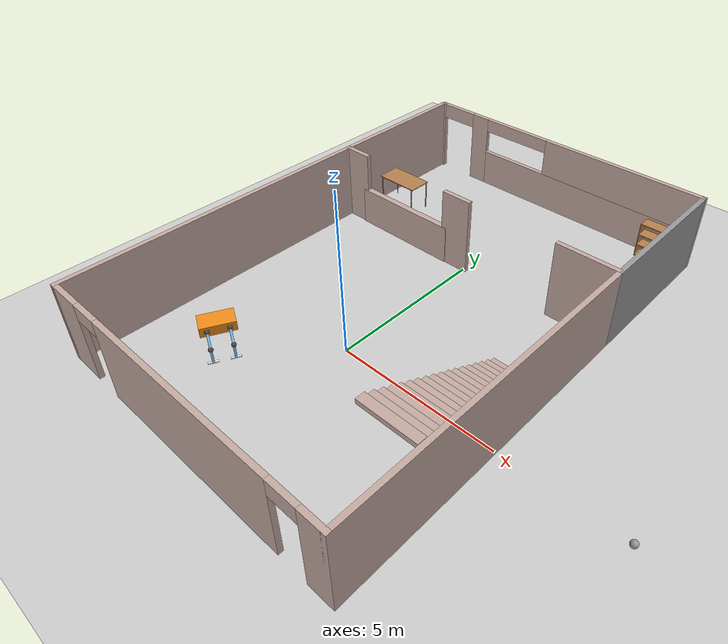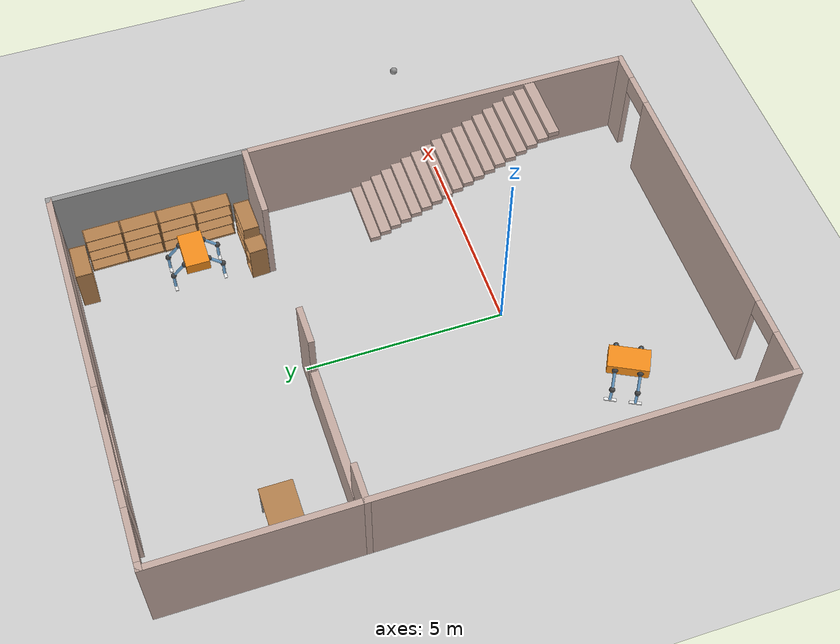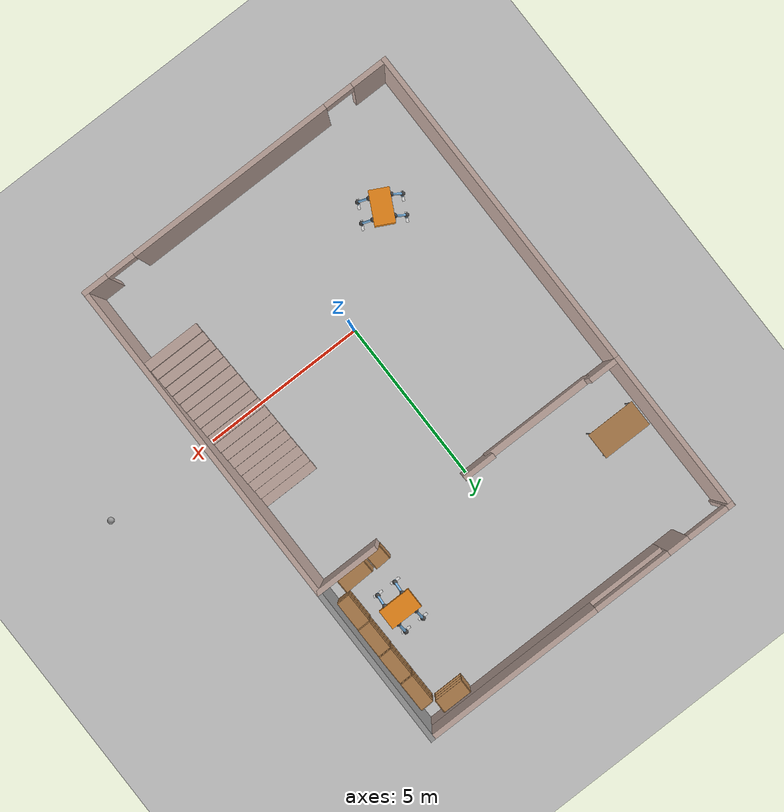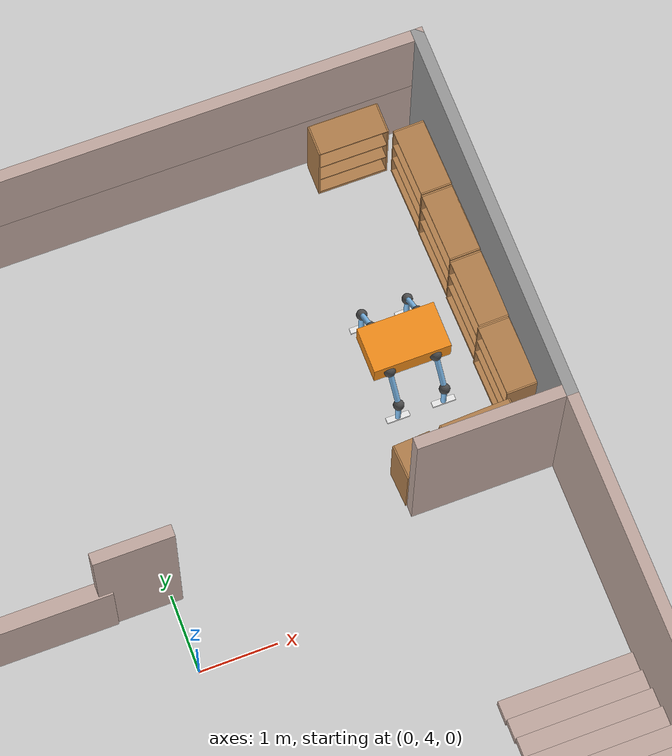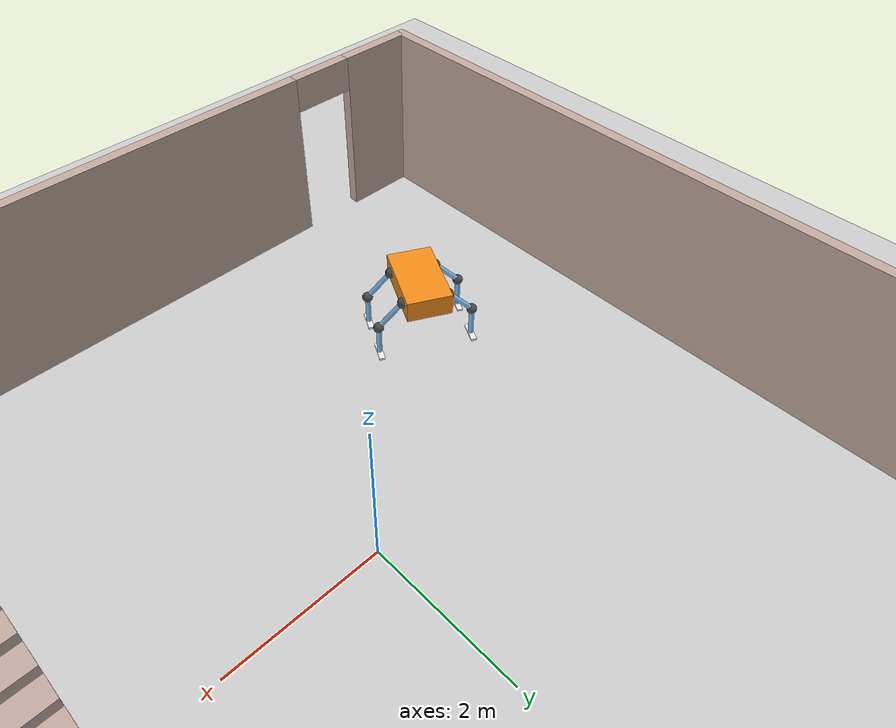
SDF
<sdf version="1.6">
 <world name="default">
  <plugin name="hello" filename="libhello.so"/>
  <light name="sun" type="directional">
   <pose>0 0 10 0 -0 0</pose>
   <diffuse>0.8 0.8 0.8 1</diffuse>
   <specular>0.2 0.2 0.2 1</specular>
   <attenuation>
    <range>1000</range>
    <constant>0.9</constant>
    <linear>0.01</linear>
    <quadratic>0.001</quadratic>
   </attenuation>
   <direction>-0.5 0.1 -0.9</direction>
  </light>
  <model name="ground_plane">
   <static>1</static>
   <link name="link">
    <collision name="collision">
     <geometry><plane><normal>0 0 1</normal><size>100 100</size></plane></geometry>
     <surface>
      <contact><collide_bitmask>65535</collide_bitmask></contact>
      <friction><ode><mu>100</mu><mu2>50</mu2></ode></friction>
     </surface>
    </collision>
    <visual name="visual">
     <cast_shadows>0</cast_shadows>
     <geometry><plane><normal>0 0 1</normal><size>100 100</size></plane></geometry>
     <material>
      <script><uri>file://media/materials/scripts/gazebo.material</uri><name>Gazebo/Grey</name></script>
     </material>
    </visual>
   </link>
  </model>
  <gravity>0 0 -9.8</gravity>
  <magnetic_field>6e-06 2.3e-05 -4.2e-05</magnetic_field>
  <atmosphere type="adiabatic"/>
  <physics name="default_physics" default="0" type="ode">
   <max_step_size>0.001</max_step_size>
   <real_time_factor>1</real_time_factor>
   <real_time_update_rate>1000</real_time_update_rate>
  </physics>
  <scene><ambient>0.4 0.4 0.4 1</ambient><background>0.7 0.7 0.7 1</background><shadows>1</shadows></scene>
  <spherical_coordinates>
   <surface_model>EARTH_WGS84</surface_model>
   <latitude_deg>0</latitude_deg>
   <longitude_deg>0</longitude_deg>
   <elevation>0</elevation>
   <heading_deg>0</heading_deg>
  </spherical_coordinates>
  <model name="Living_room">
   <pose>0 2.425 0 0 -0 0</pose>
   <link name="Stairs_2">
    <visual name="Stairs_2_Visual_0">
     <pose>4.04837 -0.186051 0.069444 0 -0 0</pose>
     <geometry><box><size>1.735 0.275167 0.138889</size></box></geometry>
     <material>
      <script><uri>file://media/materials/scripts/gazebo.material</uri><name>Gazebo/Grey</name></script>
      <ambient>0.760784 0.662745 0.627451 1</ambient>
     </material>
     <meta><layer>0</layer></meta>
    </visual>
    <collision name="Stairs_2_Collision_0">
     <geometry><box><size>1.735 0.275167 0.138889</size></box></geometry>
     <pose>4.04837 -0.186051 0.069444 0 -0 0</pose>
    </collision>
    <visual name="Stairs_2_Visual_1">
     <pose>4.04837 -0.461218 0.208333 0 -0 0</pose>
     <geometry><box><size>1.735 0.275167 0.138889</size></box></geometry>
     <material>
      <script><uri>file://media/materials/scripts/gazebo.material</uri><name>Gazebo/Grey</name></script>
      <ambient>0.760784 0.662745 0.627451 1</ambient>
     </material>
     <meta><layer>0</layer></meta>
    </visual>
    <collision name="Stairs_2_Collision_1">
     <geometry><box><size>1.735 0.275167 0.138889</size></box></geometry>
     <pose>4.04837 -0.461218 0.208333 0 -0 0</pose>
    </collision>
    <visual name="Stairs_2_Visual_2">
     <pose>4.04837 -0.736385 0.347222 0 -0 0</pose>
     <geometry><box><size>1.735 0.275167 0.138889</size></box></geometry>
     <material>
      <script><uri>file://media/materials/scripts/gazebo.material</uri><name>Gazebo/Grey</name></script>
      <ambient>0.760784 0.662745 0.627451 1</ambient>
     </material>
     <meta><layer>0</layer></meta>
    </visual>
    <collision name="Stairs_2_Collision_2">
     <geometry><box><size>1.735 0.275167 0.138889</size></box></geometry>
     <pose>4.04837 -0.736385 0.347222 0 -0 0</pose>
    </collision>
    <visual name="Stairs_2_Visual_3">
     <pose>4.04837 -1.01155 0.486111 0 -0 0</pose>
     <geometry><box><size>1.735 0.275167 0.138889</size></box></geometry>
     <material>
      <script><uri>file://media/materials/scripts/gazebo.material</uri><name>Gazebo/Grey</name></script>
      <ambient>0.760784 0.662745 0.627451 1</ambient>
     </material>
     <meta><layer>0</layer></meta>
    </visual>
    <collision name="Stairs_2_Collision_3">
     <geometry><box><size>1.735 0.275167 0.138889</size></box></geometry>
     <pose>4.04837 -1.01155 0.486111 0 -0 0</pose>
    </collision>
    <visual name="Stairs_2_Visual_4">
     <pose>4.04837 -1.28672 0.625 0 -0 0</pose>
     <geometry><box><size>1.735 0.275167 0.138889</size></box></geometry>
     <material>
      <script><uri>file://media/materials/scripts/gazebo.material</uri><name>Gazebo/Grey</name></script>
      <ambient>0.760784 0.662745 0.627451 1</ambient>
     </material>
     <meta><layer>0</layer></meta>
    </visual>
    <collision name="Stairs_2_Collision_4">
     <geometry><box><size>1.735 0.275167 0.138889</size></box></geometry>
     <pose>4.04837 -1.28672 0.625 0 -0 0</pose>
    </collision>
    <visual name="Stairs_2_Visual_5">
     <pose>4.04837 -1.56188 0.763889 0 -0 0</pose>
     <geometry><box><size>1.735 0.275167 0.138889</size></box></geometry>
     <material>
      <script><uri>file://media/materials/scripts/gazebo.material</uri><name>Gazebo/Grey</name></script>
      <ambient>0.760784 0.662745 0.627451 1</ambient>
     </material>
     <meta><layer>0</layer></meta>
    </visual>
    <collision name="Stairs_2_Collision_5">
     <geometry><box><size>1.735 0.275167 0.138889</size></box></geometry>
     <pose>4.04837 -1.56188 0.763889 0 -0 0</pose>
    </collision>
    <visual name="Stairs_2_Visual_6">
     <pose>4.04837 -1.83705 0.902778 0 -0 0</pose>
     <geometry><box><size>1.735 0.275167 0.138889</size></box></geometry>
     <material>
      <script><uri>file://media/materials/scripts/gazebo.material</uri><name>Gazebo/Grey</name></script>
      <ambient>0.760784 0.662745 0.627451 1</ambient>
     </material>
     <meta><layer>0</layer></meta>
    </visual>
    <collision name="Stairs_2_Collision_6">
     <geometry><box><size>1.735 0.275167 0.138889</size></box></geometry>
     <pose>4.04837 -1.83705 0.902778 0 -0 0</pose>
    </collision>
    <visual name="Stairs_2_Visual_7">
     <pose>4.04837 -2.11222 1.04167 0 -0 0</pose>
     <geometry><box><size>1.735 0.275167 0.138889</size></box></geometry>
     <material>
      <script><uri>file://media/materials/scripts/gazebo.material</uri><name>Gazebo/Grey</name></script>
      <ambient>0.760784 0.662745 0.627451 1</ambient>
     </material>
     <meta><layer>0</layer></meta>
    </visual>
    <collision name="Stairs_2_Collision_7">
     <geometry><box><size>1.735 0.275167 0.138889</size></box></geometry>
     <pose>4.04837 -2.11222 1.04167 0 -0 0</pose>
    </collision>
    <visual name="Stairs_2_Visual_8">
     <pose>4.04837 -2.38739 1.18056 0 -0 0</pose>
     <geometry><box><size>1.735 0.275167 0.138889</size></box></geometry>
     <material>
      <script><uri>file://media/materials/scripts/gazebo.material</uri><name>Gazebo/Grey</name></script>
      <ambient>0.760784 0.662745 0.627451 1</ambient>
     </material>
     <meta><layer>0</layer></meta>
    </visual>
    <collision name="Stairs_2_Collision_8">
     <geometry><box><size>1.735 0.275167 0.138889</size></box></geometry>
     <pose>4.04837 -2.38739 1.18056 0 -0 0</pose>
    </collision>
    <visual name="Stairs_2_Visual_9">
     <pose>4.04837 -2.66255 1.31944 0 -0 0</pose>
     <geometry><box><size>1.735 0.275167 0.138889</size></box></geometry>
     <material>
      <script><uri>file://media/materials/scripts/gazebo.material</uri><name>Gazebo/Grey</name></script>
      <ambient>0.760784 0.662745 0.627451 1</ambient>
     </material>
     <meta><layer>0</layer></meta>
    </visual>
    <collision name="Stairs_2_Collision_9">
     <geometry><box><size>1.735 0.275167 0.138889</size></box></geometry>
     <pose>4.04837 -2.66255 1.31944 0 -0 0</pose>
    </collision>
    <visual name="Stairs_2_Visual_10">
     <pose>4.04837 -2.93772 1.45833 0 -0 0</pose>
     <geometry><box><size>1.735 0.275167 0.138889</size></box></geometry>
     <material>
      <script><uri>file://media/materials/scripts/gazebo.material</uri><name>Gazebo/Grey</name></script>
      <ambient>0.760784 0.662745 0.627451 1</ambient>
     </material>
     <meta><layer>0</layer></meta>
    </visual>
    <collision name="Stairs_2_Collision_10">
     <geometry><box><size>1.735 0.275167 0.138889</size></box></geometry>
     <pose>4.04837 -2.93772 1.45833 0 -0 0</pose>
    </collision>
    <visual name="Stairs_2_Visual_11">
     <pose>4.04837 -3.21288 1.59722 0 -0 0</pose>
     <geometry><box><size>1.735 0.275167 0.138889</size></box></geometry>
     <material>
      <script><uri>file://media/materials/scripts/gazebo.material</uri><name>Gazebo/Grey</name></script>
      <ambient>0.760784 0.662745 0.627451 1</ambient>
     </material>
     <meta><layer>0</layer></meta>
    </visual>
    <collision name="Stairs_2_Collision_11">
     <geometry><box><size>1.735 0.275167 0.138889</size></box></geometry>
     <pose>4.04837 -3.21288 1.59722 0 -0 0</pose>
    </collision>
    <visual name="Stairs_2_Visual_12">
     <pose>4.04837 -3.48805 1.73611 0 -0 0</pose>
     <geometry><box><size>1.735 0.275167 0.138889</size></box></geometry>
     <material>
      <script><uri>file://media/materials/scripts/gazebo.material</uri><name>Gazebo/Grey</name></script>
      <ambient>0.760784 0.662745 0.627451 1</ambient>
     </material>
     <meta><layer>0</layer></meta>
    </visual>
    <collision name="Stairs_2_Collision_12">
     <geometry><box><size>1.735 0.275167 0.138889</size></box></geometry>
     <pose>4.04837 -3.48805 1.73611 0 -0 0</pose>
    </collision>
    <visual name="Stairs_2_Visual_13">
     <pose>4.04837 -3.76322 1.875 0 -0 0</pose>
     <geometry><box><size>1.735 0.275167 0.138889</size></box></geometry>
     <material>
      <script><uri>file://media/materials/scripts/gazebo.material</uri><name>Gazebo/Grey</name></script>
      <ambient>0.760784 0.662745 0.627451 1</ambient>
     </material>
     <meta><layer>0</layer></meta>
    </visual>
    <collision name="Stairs_2_Collision_13">
     <geometry><box><size>1.735 0.275167 0.138889</size></box></geometry>
     <pose>4.04837 -3.76322 1.875 0 -0 0</pose>
    </collision>
    <visual name="Stairs_2_Visual_14">
     <pose>4.04837 -4.03838 2.01389 0 -0 0</pose>
     <geometry><box><size>1.735 0.275167 0.138889</size></box></geometry>
     <material>
      <script><uri>file://media/materials/scripts/gazebo.material</uri><name>Gazebo/Grey</name></script>
      <ambient>0.760784 0.662745 0.627451 1</ambient>
     </material>
     <meta><layer>0</layer></meta>
    </visual>
    <collision name="Stairs_2_Collision_14">
     <geometry><box><size>1.735 0.275167 0.138889</size></box></geometry>
     <pose>4.04837 -4.03838 2.01389 0 -0 0</pose>
    </collision>
    <visual name="Stairs_2_Visual_15">
     <pose>4.04837 -4.31355 2.15278 0 -0 0</pose>
     <geometry><box><size>1.735 0.275167 0.138889</size></box></geometry>
     <material>
      <script><uri>file://media/materials/scripts/gazebo.material</uri><name>Gazebo/Grey</name></script>
      <ambient>0.760784 0.662745 0.627451 1</ambient>
     </material>
     <meta><layer>0</layer></meta>
    </visual>
    <collision name="Stairs_2_Collision_15">
     <geometry><box><size>1.735 0.275167 0.138889</size></box></geometry>
     <pose>4.04837 -4.31355 2.15278 0 -0 0</pose>
    </collision>
    <visual name="Stairs_2_Visual_16">
     <pose>4.04837 -4.58872 2.29167 0 -0 0</pose>
     <geometry><box><size>1.735 0.275167 0.138889</size></box></geometry>
     <material>
      <script><uri>file://media/materials/scripts/gazebo.material</uri><name>Gazebo/Grey</name></script>
      <ambient>0.760784 0.662745 0.627451 1</ambient>
     </material>
     <meta><layer>0</layer></meta>
    </visual>
    <collision name="Stairs_2_Collision_16">
     <geometry><box><size>1.735 0.275167 0.138889</size></box></geometry>
     <pose>4.04837 -4.58872 2.29167 0 -0 0</pose>
    </collision>
    <visual name="Stairs_2_Visual_17">
     <pose>4.04837 -4.86388 2.43056 0 -0 0</pose>
     <geometry><box><size>1.735 0.275167 0.138889</size></box></geometry>
     <material>
      <script><uri>file://media/materials/scripts/gazebo.material</uri><name>Gazebo/Grey</name></script>
      <ambient>0.760784 0.662745 0.627451 1</ambient>
     </material>
     <meta><layer>0</layer></meta>
    </visual>
    <collision name="Stairs_2_Collision_17">
     <geometry><box><size>1.735 0.275167 0.138889</size></box></geometry>
     <pose>4.04837 -4.86388 2.43056 0 -0 0</pose>
    </collision>
   </link>
   <link name="Wall_10">
    <collision name="Wall_10_Collision">
     <geometry><box><size>3.55 0.2 1.25</size></box></geometry>
     <pose>0 0 0.625 0 -0 0</pose>
    </collision>
    <visual name="Wall_10_Visual">
     <pose>0 0 0.625 0 -0 0</pose>
     <geometry><box><size>3.55 0.2 1.25</size></box></geometry>
     <material>
      <script><uri>file://media/materials/scripts/gazebo.material</uri><name>Gazebo/Grey</name></script>
      <ambient>0.760784 0.662745 0.627451 1</ambient>
     </material>
     <meta><layer>0</layer></meta>
    </visual>
    <pose>-2.475 2.575 0 0 -0 0</pose>
   </link>
   <link name="Wall_11">
    <collision name="Wall_11_Collision">
     <geometry><box><size>1 0.15 2.5</size></box></geometry>
     <pose>0 0 1.25 0 -0 0</pose>
    </collision>
    <visual name="Wall_11_Visual">
     <pose>0 0 1.25 0 -0 0</pose>
     <geometry><box><size>1 0.15 2.5</size></box></geometry>
     <material>
      <script><uri>file://media/materials/scripts/gazebo.material</uri><name>Gazebo/Grey</name></script>
      <ambient>0.760784 0.662745 0.627451 1</ambient>
     </material>
     <meta><layer>0</layer></meta>
    </visual>
    <pose>-0.375 2.575 0 0 -0 0</pose>
   </link>
   <link name="Wall_18">
    <collision name="Wall_18_Collision">
     <geometry><box><size>2 0.15 2.5</size></box></geometry>
     <pose>0 0 1.25 0 -0 0</pose>
    </collision>
    <visual name="Wall_18_Visual">
     <pose>0 0 1.25 0 -0 0</pose>
     <geometry><box><size>2 0.15 2.5</size></box></geometry>
     <material>
      <script><uri>file://media/materials/scripts/gazebo.material</uri><name>Gazebo/Grey</name></script>
      <ambient>0.760784 0.662745 0.627451 1</ambient>
     </material>
     <meta><layer>0</layer></meta>
    </visual>
    <pose>4.075 2.575 0 0 -0 3.14159</pose>
   </link>
   <link name="Wall_2">
    <collision name="Wall_2_Collision">
     <geometry><box><size>10.15 0.15 2.5</size></box></geometry>
     <pose>0 0 1.25 0 -0 0</pose>
    </collision>
    <visual name="Wall_2_Visual">
     <pose>0 0 1.25 0 -0 0</pose>
     <geometry><box><size>10.15 0.15 2.5</size></box></geometry>
     <material>
      <script><uri>file://media/materials/scripts/gazebo.material</uri><name>Gazebo/Grey</name></script>
      <ambient>0.760784 0.662745 0.627451 1</ambient>
     </material>
     <meta><layer>0</layer></meta>
    </visual>
    <pose>-5 -2.425 0 0 0 -1.5708</pose>
   </link>
   <link name="Wall_20">
    <collision name="Wall_20_Collision">
     <geometry><box><size>5 0.15 2.5</size></box></geometry>
     <pose>0 0 1.25 0 -0 0</pose>
    </collision>
    <visual name="Wall_20_Visual">
     <pose>0 0 1.25 0 -0 0</pose>
     <geometry><box><size>5 0.15 2.5</size></box></geometry>
     <material>
      <script><uri>file://media/materials/scripts/gazebo.material</uri><name>Gazebo/Grey</name></script>
      <ambient>1 1 1 1</ambient>
     </material>
     <meta><layer>0</layer></meta>
    </visual>
    <pose>5 5 0 0 -0 1.5708</pose>
   </link>
   <link name="Wall_24">
    <collision name="Wall_24_Collision">
     <geometry><box><size>5 0.15 2.5</size></box></geometry>
     <pose>0 0 1.25 0 -0 0</pose>
    </collision>
    <visual name="Wall_24_Visual">
     <pose>0 0 1.25 0 -0 0</pose>
     <geometry><box><size>5 0.15 2.5</size></box></geometry>
     <material>
      <script><uri>file://media/materials/scripts/gazebo.material</uri><name>Gazebo/Grey</name></script>
      <ambient>0.760784 0.662745 0.627451 1</ambient>
     </material>
     <meta><layer>0</layer></meta>
    </visual>
    <pose>-5 5 0 0 -0 1.5708</pose>
   </link>
   <link name="Wall_28">
    <pose>0 7.425 0 0 -0 0</pose>
    <visual name="Wall_28_Visual_0">
     <pose>-4.96565 0 1.25 0 -0 0</pose>
     <geometry><box><size>0.218693 0.15 2.5</size></box></geometry>
     <material>
      <script><uri>file://media/materials/scripts/gazebo.material</uri><name>Gazebo/Grey</name></script>
      <ambient>0.760784 0.662745 0.627451 1</ambient>
     </material>
     <meta><layer>0</layer></meta>
    </visual>
    <collision name="Wall_28_Collision_0">
     <geometry><box><size>0.218693 0.15 2.5</size></box></geometry>
     <pose>-4.96565 0 1.25 0 -0 0</pose>
    </collision>
    <visual name="Wall_28_Visual_1">
     <pose>-3.23794 0 1.25 0 -0 0</pose>
     <geometry><box><size>0.662798 0.15 2.5</size></box></geometry>
     <material>
      <script><uri>file://media/materials/scripts/gazebo.material</uri><name>Gazebo/Grey</name></script>
      <ambient>0.760784 0.662745 0.627451 1</ambient>
     </material>
     <meta><layer>0</layer></meta>
    </visual>
    <collision name="Wall_28_Collision_1">
     <geometry><box><size>0.662798 0.15 2.5</size></box></geometry>
     <pose>-3.23794 0 1.25 0 -0 0</pose>
    </collision>
    <visual name="Wall_28_Visual_2">
     <pose>1.08423 0 0.625 0 -0 0</pose>
     <geometry><box><size>7.98154 0.15 1.25</size></box></geometry>
     <material>
      <script><uri>file://media/materials/scripts/gazebo.material</uri><name>Gazebo/Grey</name></script>
      <ambient>0.760784 0.662745 0.627451 1</ambient>
     </material>
     <meta><layer>0</layer></meta>
    </visual>
    <collision name="Wall_28_Collision_2">
     <geometry><box><size>7.98154 0.15 1.25</size></box></geometry>
     <pose>1.08423 0 0.625 0 -0 0</pose>
    </collision>
    <visual name="Wall_28_Visual_3">
     <pose>2.29323 0 1.875 0 -0 0</pose>
     <geometry><box><size>5.56354 0.15 1.25</size></box></geometry>
     <material>
      <script><uri>file://media/materials/scripts/gazebo.material</uri><name>Gazebo/Grey</name></script>
      <ambient>0.760784 0.662745 0.627451 1</ambient>
     </material>
     <meta><layer>0</layer></meta>
    </visual>
    <collision name="Wall_28_Collision_3">
     <geometry><box><size>5.56354 0.15 1.25</size></box></geometry>
     <pose>2.29323 0 1.875 0 -0 0</pose>
    </collision>
    <visual name="Wall_28_Visual_4">
     <pose>-4.21282 0 2.25 0 -0 0</pose>
     <geometry><box><size>1.28697 0.15 0.5</size></box></geometry>
     <material>
      <script><uri>file://media/materials/scripts/gazebo.material</uri><name>Gazebo/Grey</name></script>
      <ambient>0.760784 0.662745 0.627451 1</ambient>
     </material>
     <meta><layer>0</layer></meta>
    </visual>
    <collision name="Wall_28_Collision_4">
     <geometry><box><size>1.28697 0.15 0.5</size></box></geometry>
     <pose>-4.21282 0 2.25 0 -0 0</pose>
    </collision>
    <visual name="Wall_28_Visual_5">
     <pose>-1.69754 0 2.275 0 -0 0</pose>
     <geometry><box><size>2.418 0.15 0.45</size></box></geometry>
     <material>
      <script><uri>file://media/materials/scripts/gazebo.material</uri><name>Gazebo/Grey</name></script>
      <ambient>0.760784 0.662745 0.627451 1</ambient>
     </material>
     <meta><layer>0</layer></meta>
    </visual>
    <collision name="Wall_28_Collision_5">
     <geometry><box><size>2.418 0.15 0.45</size></box></geometry>
     <pose>-1.69754 0 2.275 0 -0 0</pose>
    </collision>
   </link>
   <link name="Wall_3">
    <pose>0 -7.425 0 0 -0 0</pose>
    <visual name="Wall_3_Visual_0">
     <pose>-4.48861 0 1.25 0 -0 0</pose>
     <geometry><box><size>1.17278 0.15 2.5</size></box></geometry>
     <material>
      <script><uri>file://media/materials/scripts/gazebo.material</uri><name>Gazebo/Grey</name></script>
      <ambient>0.760784 0.662745 0.627451 1</ambient>
     </material>
     <meta><layer>0</layer></meta>
    </visual>
    <collision name="Wall_3_Collision_0">
     <geometry><box><size>1.17278 0.15 2.5</size></box></geometry>
     <pose>-4.48861 0 1.25 0 -0 0</pose>
    </collision>
    <visual name="Wall_3_Visual_1">
     <pose>0.186013 0 1.25 0 -0 0</pose>
     <geometry><box><size>6.37646 0.15 2.5</size></box></geometry>
     <material>
      <script><uri>file://media/materials/scripts/gazebo.material</uri><name>Gazebo/Grey</name></script>
      <ambient>0.760784 0.662745 0.627451 1</ambient>
     </material>
     <meta><layer>0</layer></meta>
    </visual>
    <collision name="Wall_3_Collision_1">
     <geometry><box><size>6.37646 0.15 2.5</size></box></geometry>
     <pose>0.186013 0 1.25 0 -0 0</pose>
    </collision>
    <visual name="Wall_3_Visual_2">
     <pose>4.67462 0 1.25 0 -0 0</pose>
     <geometry><box><size>0.800759 0.15 2.5</size></box></geometry>
     <material>
      <script><uri>file://media/materials/scripts/gazebo.material</uri><name>Gazebo/Grey</name></script>
      <ambient>0.760784 0.662745 0.627451 1</ambient>
     </material>
     <meta><layer>0</layer></meta>
    </visual>
    <collision name="Wall_3_Collision_2">
     <geometry><box><size>0.800759 0.15 2.5</size></box></geometry>
     <pose>4.67462 0 1.25 0 -0 0</pose>
    </collision>
    <visual name="Wall_3_Visual_3">
     <pose>-3.45221 0 2.25 0 -0 0</pose>
     <geometry><box><size>0.9 0.15 0.5</size></box></geometry>
     <material>
      <script><uri>file://media/materials/scripts/gazebo.material</uri><name>Gazebo/Grey</name></script>
      <ambient>0.760784 0.662745 0.627451 1</ambient>
     </material>
     <meta><layer>0</layer></meta>
    </visual>
    <collision name="Wall_3_Collision_3">
     <geometry><box><size>0.9 0.15 0.5</size></box></geometry>
     <pose>-3.45221 0 2.25 0 -0 0</pose>
    </collision>
    <visual name="Wall_3_Visual_4">
     <pose>3.82424 0 2.25 0 -0 0</pose>
     <geometry><box><size>0.9 0.15 0.5</size></box></geometry>
     <material>
      <script><uri>file://media/materials/scripts/gazebo.material</uri><name>Gazebo/Grey</name></script>
      <ambient>0.760784 0.662745 0.627451 1</ambient>
     </material>
     <meta><layer>0</layer></meta>
    </visual>
    <collision name="Wall_3_Collision_4">
     <geometry><box><size>0.9 0.15 0.5</size></box></geometry>
     <pose>3.82424 0 2.25 0 -0 0</pose>
    </collision>
   </link>
   <link name="Wall_4">
    <collision name="Wall_4_Collision">
     <geometry><box><size>10.15 0.15 2.5</size></box></geometry>
     <pose>0 0 1.25 0 -0 0</pose>
    </collision>
    <visual name="Wall_4_Visual">
     <pose>0 0 1.25 0 -0 0</pose>
     <geometry><box><size>10.15 0.15 2.5</size></box></geometry>
     <material>
      <script><uri>file://media/materials/scripts/gazebo.material</uri><name>Gazebo/Grey</name></script>
      <ambient>0.760784 0.662745 0.627451 1</ambient>
     </material>
     <meta><layer>0</layer></meta>
    </visual>
    <pose>5 -2.425 0 0 -0 1.5708</pose>
   </link>
   <link name="Wall_9">
    <collision name="Wall_9_Collision">
     <geometry><box><size>1 0.15 2.5</size></box></geometry>
     <pose>0 0 1.25 0 -0 0</pose>
    </collision>
    <visual name="Wall_9_Visual">
     <pose>0 0 1.25 0 -0 0</pose>
     <geometry><box><size>1 0.15 2.5</size></box></geometry>
     <material>
      <script><uri>file://media/materials/scripts/gazebo.material</uri><name>Gazebo/Grey</name></script>
      <ambient>0.760784 0.662745 0.627451 1</ambient>
     </material>
     <meta><layer>0</layer></meta>
    </visual>
    <pose>-4.575 2.575 0 0 -0 0</pose>
   </link>
   <static>1</static>
  </model>
  <model name="table">
   <static>1</static>
   <link name="link">
    <collision name="surface">
     <pose>0 0 1 0 -0 0</pose>
     <geometry><box><size>1.5 0.8 0.03</size></box></geometry>
     <surface><friction><ode><mu>0.6</mu><mu2>0.6</mu2></ode></friction></surface>
    </collision>
    <visual name="visual1">
     <pose>0 0 1 0 -0 0</pose>
     <geometry><box><size>1.5 0.8 0.03</size></box></geometry>
     <material>
      <script><uri>file://media/materials/scripts/gazebo.material</uri><name>Gazebo/Wood</name></script>
     </material>
    </visual>
    <collision name="front_left_leg">
     <pose>0.68 0.38 0.5 0 -0 0</pose>
     <geometry><cylinder><radius>0.02</radius><length>1</length></cylinder></geometry>
    </collision>
    <visual name="front_left_leg">
     <pose>0.68 0.38 0.5 0 -0 0</pose>
     <geometry><cylinder><radius>0.02</radius><length>1</length></cylinder></geometry>
     <material>
      <script><uri>file://media/materials/scripts/gazebo.material</uri><name>Gazebo/Grey</name></script>
     </material>
    </visual>
    <collision name="front_right_leg">
     <pose>0.68 -0.38 0.5 0 -0 0</pose>
     <geometry><cylinder><radius>0.02</radius><length>1</length></cylinder></geometry>
    </collision>
    <visual name="front_right_leg">
     <pose>0.68 -0.38 0.5 0 -0 0</pose>
     <geometry><cylinder><radius>0.02</radius><length>1</length></cylinder></geometry>
     <material>
      <script><uri>file://media/materials/scripts/gazebo.material</uri><name>Gazebo/Grey</name></script>
     </material>
    </visual>
    <collision name="back_right_leg">
     <pose>-0.68 -0.38 0.5 0 -0 0</pose>
     <geometry><cylinder><radius>0.02</radius><length>1</length></cylinder></geometry>
    </collision>
    <visual name="back_right_leg">
     <pose>-0.68 -0.38 0.5 0 -0 0</pose>
     <geometry><cylinder><radius>0.02</radius><length>1</length></cylinder></geometry>
     <material>
      <script><uri>file://media/materials/scripts/gazebo.material</uri><name>Gazebo/Grey</name></script>
     </material>
    </visual>
    <collision name="back_left_leg">
     <pose>-0.68 0.38 0.5 0 -0 0</pose>
     <geometry><cylinder><radius>0.02</radius><length>1</length></cylinder></geometry>
    </collision>
    <visual name="back_left_leg">
     <pose>-0.68 0.38 0.5 0 -0 0</pose>
     <geometry><cylinder><radius>0.02</radius><length>1</length></cylinder></geometry>
     <material>
      <script><uri>file://media/materials/scripts/gazebo.material</uri><name>Gazebo/Grey</name></script>
     </material>
    </visual>
   </link>
   <pose>-4.01513 6.60986 0 0 -0 0</pose>
  </model>
  <model name="bookshelf">
   <static>1</static>
   <link name="link">
    <inertial><mass>1</mass></inertial>
    <collision name="back">
     <pose>0 0.005 0.6 0 -0 0</pose>
     <geometry><box><size>0.9 0.01 1.2</size></box></geometry>
    </collision>
    <visual name="visual1">
     <pose>0 0.005 0.6 0 -0 0</pose>
     <geometry><box><size>0.9 0.01 1.2</size></box></geometry>
     <material>
      <script><uri>file://media/materials/scripts/gazebo.material</uri><name>Gazebo/Wood</name></script>
     </material>
    </visual>
    <collision name="left_side">
     <pose>0.45 -0.195 0.6 0 -0 0</pose>
     <geometry><box><size>0.02 0.4 1.2</size></box></geometry>
    </collision>
    <visual name="visual2">
     <pose>0.45 -0.195 0.6 0 -0 0</pose>
     <geometry><box><size>0.02 0.4 1.2</size></box></geometry>
     <material>
      <script><uri>file://media/materials/scripts/gazebo.material</uri><name>Gazebo/Wood</name></script>
     </material>
    </visual>
    <collision name="right_side">
     <pose>-0.45 -0.195 0.6 0 -0 0</pose>
     <geometry><box><size>0.02 0.4 1.2</size></box></geometry>
    </collision>
    <visual name="visual3">
     <pose>-0.45 -0.195 0.6 0 -0 0</pose>
     <geometry><box><size>0.02 0.4 1.2</size></box></geometry>
     <material>
      <script><uri>file://media/materials/scripts/gazebo.material</uri><name>Gazebo/Wood</name></script>
     </material>
    </visual>
    <collision name="bottom">
     <pose>0 -0.195 0.03 0 -0 0</pose>
     <geometry><box><size>0.88 0.4 0.06</size></box></geometry>
    </collision>
    <visual name="visual4">
     <pose>0 -0.195 0.03 0 -0 0</pose>
     <geometry><box><size>0.88 0.4 0.06</size></box></geometry>
     <material>
      <script><uri>file://media/materials/scripts/gazebo.material</uri><name>Gazebo/Wood</name></script>
     </material>
    </visual>
    <collision name="top">
     <pose>0 -0.195 1.19 0 -0 0</pose>
     <geometry><box><size>0.88 0.4 0.02</size></box></geometry>
    </collision>
    <visual name="visual5">
     <pose>0 -0.195 1.19 0 -0 0</pose>
     <geometry><box><size>0.88 0.4 0.02</size></box></geometry>
     <material>
      <script><uri>file://media/materials/scripts/gazebo.material</uri><name>Gazebo/Wood</name></script>
     </material>
    </visual>
    <collision name="low_shelf">
     <pose>0 -0.195 0.43 0 -0 0</pose>
     <geometry><box><size>0.88 0.4 0.02</size></box></geometry>
    </collision>
    <visual name="visual6">
     <pose>0 -0.195 0.43 0 -0 0</pose>
     <geometry><box><size>0.88 0.4 0.02</size></box></geometry>
     <material>
      <script><uri>file://media/materials/scripts/gazebo.material</uri><name>Gazebo/Wood</name></script>
     </material>
    </visual>
    <collision name="high_shelf">
     <pose>0 -0.195 0.8 0 -0 0</pose>
     <geometry><box><size>0.88 0.4 0.02</size></box></geometry>
    </collision>
    <visual name="visual7">
     <pose>0 -0.195 0.8 0 -0 0</pose>
     <geometry><box><size>0.88 0.4 0.02</size></box></geometry>
     <material>
      <script><uri>file://media/materials/scripts/gazebo.material</uri><name>Gazebo/Wood</name></script>
     </material>
    </visual>
   </link>
   <pose>3.98709 9.71457 0 0 -0 0</pose>
  </model>
  <model name="cabinet">
   <static>1</static>
   <link name="cabinet_bottom_plate">
    <inertial>
     <pose>0 0 -1 0 -0 0</pose>
     <inertia><ixx>2.05</ixx><ixy>0</ixy><ixz>0</ixz><iyy>2.05</iyy><iyz>0</iyz><izz>2.05</izz></inertia>
     <mass>25</mass>
    </inertial>
    <collision name="cabinet_bottom_plate_geom">
     <pose>0 0 0.01 0 -0 0</pose>
     <geometry><box><size>0.45 0.45 0.02</size></box></geometry>
    </collision>
    <visual name="cabinet_bottom_plate_geom_visual">
     <pose>0 0 0.01 0 -0 0</pose>
     <geometry><box><size>0.45 0.45 0.02</size></box></geometry>
     <material>
      <script><uri>file://media/materials/scripts/gazebo.material</uri><name>Gazebo/Wood</name></script>
     </material>
    </visual>
    <collision name="cabinet_bottom_plate_geom_cabinet_back_plate">
     <pose>0.235 0 0.51 0 -0 0</pose>
     <geometry><box><size>0.02 0.45 1.02</size></box></geometry>
    </collision>
    <visual name="cabinet_bottom_plate_geom_cabinet_back_plate_visual">
     <pose>0.235 0 0.51 0 -0 0</pose>
     <geometry><box><size>0.02 0.45 1.02</size></box></geometry>
     <material>
      <script><uri>file://media/materials/scripts/gazebo.material</uri><name>Gazebo/Wood</name></script>
     </material>
    </visual>
    <collision name="cabinet_bottom_plate_geom_cabinet_left_plate">
     <pose>0 0.235 0.51 0 -0 0</pose>
     <geometry><box><size>0.45 0.02 1.02</size></box></geometry>
    </collision>
    <visual name="cabinet_bottom_plate_geom_cabinet_left_plate_visual">
     <pose>0 0.235 0.51 0 -0 0</pose>
     <geometry><box><size>0.45 0.02 1.02</size></box></geometry>
     <material>
      <script><uri>file://media/materials/scripts/gazebo.material</uri><name>Gazebo/Wood</name></script>
     </material>
    </visual>
    <collision name="cabinet_bottom_plate_geom_cabinet_middle_plate">
     <pose>0 0 0.51 0 -0 0</pose>
     <geometry><box><size>0.45 0.45 0.02</size></box></geometry>
    </collision>
    <visual name="cabinet_bottom_plate_geom_cabinet_middle_plate_visual">
     <pose>0 0 0.51 0 -0 0</pose>
     <geometry><box><size>0.45 0.45 0.02</size></box></geometry>
     <material>
      <script><uri>file://media/materials/scripts/gazebo.material</uri><name>Gazebo/Wood</name></script>
     </material>
    </visual>
    <collision name="cabinet_bottom_plate_geom_cabinet_right_plate">
     <pose>0 -0.235 0.51 0 -0 0</pose>
     <geometry><box><size>0.45 0.02 1.02</size></box></geometry>
    </collision>
    <visual name="cabinet_bottom_plate_geom_cabinet_right_plate_visual">
     <pose>0 -0.235 0.51 0 -0 0</pose>
     <geometry><box><size>0.45 0.02 1.02</size></box></geometry>
     <material>
      <script><uri>file://media/materials/scripts/gazebo.material</uri><name>Gazebo/Wood</name></script>
     </material>
    </visual>
    <collision name="cabinet_bottom_plate_geom_cabinet_top_plate">
     <pose>0 0 1.01 0 -0 0</pose>
     <geometry><box><size>0.45 0.45 0.02</size></box></geometry>
    </collision>
    <visual name="cabinet_bottom_plate_geom_cabinet_top_plate_visual">
     <pose>0 0 1.01 0 -0 0</pose>
     <geometry><box><size>0.45 0.45 0.02</size></box></geometry>
     <material>
      <script><uri>file://media/materials/scripts/gazebo.material</uri><name>Gazebo/Wood</name></script>
     </material>
    </visual>
   </link>
   <pose>3.29061 5.31779 0 0 0 -1.51731</pose>
  </model>
  <model name="bookshelf_clone">
   <static>1</static>
   <link name="link">
    <inertial><mass>1</mass></inertial>
    <collision name="back">
     <pose>0 0.005 0.6 0 -0 0</pose>
     <geometry><box><size>0.9 0.01 1.2</size></box></geometry>
    </collision>
    <visual name="visual1">
     <pose>0 0.005 0.6 0 -0 0</pose>
     <geometry><box><size>0.9 0.01 1.2</size></box></geometry>
     <material>
      <script><uri>file://media/materials/scripts/gazebo.material</uri><name>Gazebo/Wood</name></script>
     </material>
    </visual>
    <collision name="left_side">
     <pose>0.45 -0.195 0.6 0 -0 0</pose>
     <geometry><box><size>0.02 0.4 1.2</size></box></geometry>
    </collision>
    <visual name="visual2">
     <pose>0.45 -0.195 0.6 0 -0 0</pose>
     <geometry><box><size>0.02 0.4 1.2</size></box></geometry>
     <material>
      <script><uri>file://media/materials/scripts/gazebo.material</uri><name>Gazebo/Wood</name></script>
     </material>
    </visual>
    <collision name="right_side">
     <pose>-0.45 -0.195 0.6 0 -0 0</pose>
     <geometry><box><size>0.02 0.4 1.2</size></box></geometry>
    </collision>
    <visual name="visual3">
     <pose>-0.45 -0.195 0.6 0 -0 0</pose>
     <geometry><box><size>0.02 0.4 1.2</size></box></geometry>
     <material>
      <script><uri>file://media/materials/scripts/gazebo.material</uri><name>Gazebo/Wood</name></script>
     </material>
    </visual>
    <collision name="bottom">
     <pose>0 -0.195 0.03 0 -0 0</pose>
     <geometry><box><size>0.88 0.4 0.06</size></box></geometry>
    </collision>
    <visual name="visual4">
     <pose>0 -0.195 0.03 0 -0 0</pose>
     <geometry><box><size>0.88 0.4 0.06</size></box></geometry>
     <material>
      <script><uri>file://media/materials/scripts/gazebo.material</uri><name>Gazebo/Wood</name></script>
     </material>
    </visual>
    <collision name="top">
     <pose>0 -0.195 1.19 0 -0 0</pose>
     <geometry><box><size>0.88 0.4 0.02</size></box></geometry>
    </collision>
    <visual name="visual5">
     <pose>0 -0.195 1.19 0 -0 0</pose>
     <geometry><box><size>0.88 0.4 0.02</size></box></geometry>
     <material>
      <script><uri>file://media/materials/scripts/gazebo.material</uri><name>Gazebo/Wood</name></script>
     </material>
    </visual>
    <collision name="low_shelf">
     <pose>0 -0.195 0.43 0 -0 0</pose>
     <geometry><box><size>0.88 0.4 0.02</size></box></geometry>
    </collision>
    <visual name="visual6">
     <pose>0 -0.195 0.43 0 -0 0</pose>
     <geometry><box><size>0.88 0.4 0.02</size></box></geometry>
     <material>
      <script><uri>file://media/materials/scripts/gazebo.material</uri><name>Gazebo/Wood</name></script>
     </material>
    </visual>
    <collision name="high_shelf">
     <pose>0 -0.195 0.8 0 -0 0</pose>
     <geometry><box><size>0.88 0.4 0.02</size></box></geometry>
    </collision>
    <visual name="visual7">
     <pose>0 -0.195 0.8 0 -0 0</pose>
     <geometry><box><size>0.88 0.4 0.02</size></box></geometry>
     <material>
      <script><uri>file://media/materials/scripts/gazebo.material</uri><name>Gazebo/Wood</name></script>
     </material>
    </visual>
   </link>
   <pose>4.89771 8.84904 0 0 0 -1.55013</pose>
  </model>
  <model name="bookshelf_clone_clone">
   <static>1</static>
   <link name="link">
    <inertial><mass>1</mass></inertial>
    <collision name="back">
     <pose>0 0.005 0.6 0 -0 0</pose>
     <geometry><box><size>0.9 0.01 1.2</size></box></geometry>
    </collision>
    <visual name="visual1">
     <pose>0 0.005 0.6 0 -0 0</pose>
     <geometry><box><size>0.9 0.01 1.2</size></box></geometry>
     <material>
      <script><uri>file://media/materials/scripts/gazebo.material</uri><name>Gazebo/Wood</name></script>
     </material>
    </visual>
    <collision name="left_side">
     <pose>0.45 -0.195 0.6 0 -0 0</pose>
     <geometry><box><size>0.02 0.4 1.2</size></box></geometry>
    </collision>
    <visual name="visual2">
     <pose>0.45 -0.195 0.6 0 -0 0</pose>
     <geometry><box><size>0.02 0.4 1.2</size></box></geometry>
     <material>
      <script><uri>file://media/materials/scripts/gazebo.material</uri><name>Gazebo/Wood</name></script>
     </material>
    </visual>
    <collision name="right_side">
     <pose>-0.45 -0.195 0.6 0 -0 0</pose>
     <geometry><box><size>0.02 0.4 1.2</size></box></geometry>
    </collision>
    <visual name="visual3">
     <pose>-0.45 -0.195 0.6 0 -0 0</pose>
     <geometry><box><size>0.02 0.4 1.2</size></box></geometry>
     <material>
      <script><uri>file://media/materials/scripts/gazebo.material</uri><name>Gazebo/Wood</name></script>
     </material>
    </visual>
    <collision name="bottom">
     <pose>0 -0.195 0.03 0 -0 0</pose>
     <geometry><box><size>0.88 0.4 0.06</size></box></geometry>
    </collision>
    <visual name="visual4">
     <pose>0 -0.195 0.03 0 -0 0</pose>
     <geometry><box><size>0.88 0.4 0.06</size></box></geometry>
     <material>
      <script><uri>file://media/materials/scripts/gazebo.material</uri><name>Gazebo/Wood</name></script>
     </material>
    </visual>
    <collision name="top">
     <pose>0 -0.195 1.19 0 -0 0</pose>
     <geometry><box><size>0.88 0.4 0.02</size></box></geometry>
    </collision>
    <visual name="visual5">
     <pose>0 -0.195 1.19 0 -0 0</pose>
     <geometry><box><size>0.88 0.4 0.02</size></box></geometry>
     <material>
      <script><uri>file://media/materials/scripts/gazebo.material</uri><name>Gazebo/Wood</name></script>
     </material>
    </visual>
    <collision name="low_shelf">
     <pose>0 -0.195 0.43 0 -0 0</pose>
     <geometry><box><size>0.88 0.4 0.02</size></box></geometry>
    </collision>
    <visual name="visual6">
     <pose>0 -0.195 0.43 0 -0 0</pose>
     <geometry><box><size>0.88 0.4 0.02</size></box></geometry>
     <material>
      <script><uri>file://media/materials/scripts/gazebo.material</uri><name>Gazebo/Wood</name></script>
     </material>
    </visual>
    <collision name="high_shelf">
     <pose>0 -0.195 0.8 0 -0 0</pose>
     <geometry><box><size>0.88 0.4 0.02</size></box></geometry>
    </collision>
    <visual name="visual7">
     <pose>0 -0.195 0.8 0 -0 0</pose>
     <geometry><box><size>0.88 0.4 0.02</size></box></geometry>
     <material>
      <script><uri>file://media/materials/scripts/gazebo.material</uri><name>Gazebo/Wood</name></script>
     </material>
    </visual>
   </link>
   <pose>4.91193 7.92091 0 0 0 -1.55013</pose>
  </model>
  <model name="bookshelf_clone_clone_0">
   <static>1</static>
   <link name="link">
    <inertial><mass>1</mass></inertial>
    <collision name="back">
     <pose>0 0.005 0.6 0 -0 0</pose>
     <geometry><box><size>0.9 0.01 1.2</size></box></geometry>
    </collision>
    <visual name="visual1">
     <pose>0 0.005 0.6 0 -0 0</pose>
     <geometry><box><size>0.9 0.01 1.2</size></box></geometry>
     <material>
      <script><uri>file://media/materials/scripts/gazebo.material</uri><name>Gazebo/Wood</name></script>
     </material>
    </visual>
    <collision name="left_side">
     <pose>0.45 -0.195 0.6 0 -0 0</pose>
     <geometry><box><size>0.02 0.4 1.2</size></box></geometry>
    </collision>
    <visual name="visual2">
     <pose>0.45 -0.195 0.6 0 -0 0</pose>
     <geometry><box><size>0.02 0.4 1.2</size></box></geometry>
     <material>
      <script><uri>file://media/materials/scripts/gazebo.material</uri><name>Gazebo/Wood</name></script>
     </material>
    </visual>
    <collision name="right_side">
     <pose>-0.45 -0.195 0.6 0 -0 0</pose>
     <geometry><box><size>0.02 0.4 1.2</size></box></geometry>
    </collision>
    <visual name="visual3">
     <pose>-0.45 -0.195 0.6 0 -0 0</pose>
     <geometry><box><size>0.02 0.4 1.2</size></box></geometry>
     <material>
      <script><uri>file://media/materials/scripts/gazebo.material</uri><name>Gazebo/Wood</name></script>
     </material>
    </visual>
    <collision name="bottom">
     <pose>0 -0.195 0.03 0 -0 0</pose>
     <geometry><box><size>0.88 0.4 0.06</size></box></geometry>
    </collision>
    <visual name="visual4">
     <pose>0 -0.195 0.03 0 -0 0</pose>
     <geometry><box><size>0.88 0.4 0.06</size></box></geometry>
     <material>
      <script><uri>file://media/materials/scripts/gazebo.material</uri><name>Gazebo/Wood</name></script>
     </material>
    </visual>
    <collision name="top">
     <pose>0 -0.195 1.19 0 -0 0</pose>
     <geometry><box><size>0.88 0.4 0.02</size></box></geometry>
    </collision>
    <visual name="visual5">
     <pose>0 -0.195 1.19 0 -0 0</pose>
     <geometry><box><size>0.88 0.4 0.02</size></box></geometry>
     <material>
      <script><uri>file://media/materials/scripts/gazebo.material</uri><name>Gazebo/Wood</name></script>
     </material>
    </visual>
    <collision name="low_shelf">
     <pose>0 -0.195 0.43 0 -0 0</pose>
     <geometry><box><size>0.88 0.4 0.02</size></box></geometry>
    </collision>
    <visual name="visual6">
     <pose>0 -0.195 0.43 0 -0 0</pose>
     <geometry><box><size>0.88 0.4 0.02</size></box></geometry>
     <material>
      <script><uri>file://media/materials/scripts/gazebo.material</uri><name>Gazebo/Wood</name></script>
     </material>
    </visual>
    <collision name="high_shelf">
     <pose>0 -0.195 0.8 0 -0 0</pose>
     <geometry><box><size>0.88 0.4 0.02</size></box></geometry>
    </collision>
    <visual name="visual7">
     <pose>0 -0.195 0.8 0 -0 0</pose>
     <geometry><box><size>0.88 0.4 0.02</size></box></geometry>
     <material>
      <script><uri>file://media/materials/scripts/gazebo.material</uri><name>Gazebo/Wood</name></script>
     </material>
    </visual>
   </link>
   <pose>4.91984 6.99164 0 0 0 -1.55013</pose>
  </model>
  <model name="bookshelf_clone_clone_1">
   <static>1</static>
   <link name="link">
    <inertial><mass>1</mass></inertial>
    <collision name="back">
     <pose>0 0.005 0.6 0 -0 0</pose>
     <geometry><box><size>0.9 0.01 1.2</size></box></geometry>
    </collision>
    <visual name="visual1">
     <pose>0 0.005 0.6 0 -0 0</pose>
     <geometry><box><size>0.9 0.01 1.2</size></box></geometry>
     <material>
      <script><uri>file://media/materials/scripts/gazebo.material</uri><name>Gazebo/Wood</name></script>
     </material>
    </visual>
    <collision name="left_side">
     <pose>0.45 -0.195 0.6 0 -0 0</pose>
     <geometry><box><size>0.02 0.4 1.2</size></box></geometry>
    </collision>
    <visual name="visual2">
     <pose>0.45 -0.195 0.6 0 -0 0</pose>
     <geometry><box><size>0.02 0.4 1.2</size></box></geometry>
     <material>
      <script><uri>file://media/materials/scripts/gazebo.material</uri><name>Gazebo/Wood</name></script>
     </material>
    </visual>
    <collision name="right_side">
     <pose>-0.45 -0.195 0.6 0 -0 0</pose>
     <geometry><box><size>0.02 0.4 1.2</size></box></geometry>
    </collision>
    <visual name="visual3">
     <pose>-0.45 -0.195 0.6 0 -0 0</pose>
     <geometry><box><size>0.02 0.4 1.2</size></box></geometry>
     <material>
      <script><uri>file://media/materials/scripts/gazebo.material</uri><name>Gazebo/Wood</name></script>
     </material>
    </visual>
    <collision name="bottom">
     <pose>0 -0.195 0.03 0 -0 0</pose>
     <geometry><box><size>0.88 0.4 0.06</size></box></geometry>
    </collision>
    <visual name="visual4">
     <pose>0 -0.195 0.03 0 -0 0</pose>
     <geometry><box><size>0.88 0.4 0.06</size></box></geometry>
     <material>
      <script><uri>file://media/materials/scripts/gazebo.material</uri><name>Gazebo/Wood</name></script>
     </material>
    </visual>
    <collision name="top">
     <pose>0 -0.195 1.19 0 -0 0</pose>
     <geometry><box><size>0.88 0.4 0.02</size></box></geometry>
    </collision>
    <visual name="visual5">
     <pose>0 -0.195 1.19 0 -0 0</pose>
     <geometry><box><size>0.88 0.4 0.02</size></box></geometry>
     <material>
      <script><uri>file://media/materials/scripts/gazebo.material</uri><name>Gazebo/Wood</name></script>
     </material>
    </visual>
    <collision name="low_shelf">
     <pose>0 -0.195 0.43 0 -0 0</pose>
     <geometry><box><size>0.88 0.4 0.02</size></box></geometry>
    </collision>
    <visual name="visual6">
     <pose>0 -0.195 0.43 0 -0 0</pose>
     <geometry><box><size>0.88 0.4 0.02</size></box></geometry>
     <material>
      <script><uri>file://media/materials/scripts/gazebo.material</uri><name>Gazebo/Wood</name></script>
     </material>
    </visual>
    <collision name="high_shelf">
     <pose>0 -0.195 0.8 0 -0 0</pose>
     <geometry><box><size>0.88 0.4 0.02</size></box></geometry>
    </collision>
    <visual name="visual7">
     <pose>0 -0.195 0.8 0 -0 0</pose>
     <geometry><box><size>0.88 0.4 0.02</size></box></geometry>
     <material>
      <script><uri>file://media/materials/scripts/gazebo.material</uri><name>Gazebo/Wood</name></script>
     </material>
    </visual>
   </link>
   <pose>4.91854 6.07126 0 0 0 -1.55013</pose>
  </model>
  <model name="bookshelf_clone_0">
   <static>1</static>
   <link name="link">
    <inertial><mass>1</mass></inertial>
    <collision name="back">
     <pose>0 0.005 0.6 0 -0 0</pose>
     <geometry><box><size>0.9 0.01 1.2</size></box></geometry>
    </collision>
    <visual name="visual1">
     <pose>0 0.005 0.6 0 -0 0</pose>
     <geometry><box><size>0.9 0.01 1.2</size></box></geometry>
     <material>
      <script><uri>file://media/materials/scripts/gazebo.material</uri><name>Gazebo/Wood</name></script>
     </material>
    </visual>
    <collision name="left_side">
     <pose>0.45 -0.195 0.6 0 -0 0</pose>
     <geometry><box><size>0.02 0.4 1.2</size></box></geometry>
    </collision>
    <visual name="visual2">
     <pose>0.45 -0.195 0.6 0 -0 0</pose>
     <geometry><box><size>0.02 0.4 1.2</size></box></geometry>
     <material>
      <script><uri>file://media/materials/scripts/gazebo.material</uri><name>Gazebo/Wood</name></script>
     </material>
    </visual>
    <collision name="right_side">
     <pose>-0.45 -0.195 0.6 0 -0 0</pose>
     <geometry><box><size>0.02 0.4 1.2</size></box></geometry>
    </collision>
    <visual name="visual3">
     <pose>-0.45 -0.195 0.6 0 -0 0</pose>
     <geometry><box><size>0.02 0.4 1.2</size></box></geometry>
     <material>
      <script><uri>file://media/materials/scripts/gazebo.material</uri><name>Gazebo/Wood</name></script>
     </material>
    </visual>
    <collision name="bottom">
     <pose>0 -0.195 0.03 0 -0 0</pose>
     <geometry><box><size>0.88 0.4 0.06</size></box></geometry>
    </collision>
    <visual name="visual4">
     <pose>0 -0.195 0.03 0 -0 0</pose>
     <geometry><box><size>0.88 0.4 0.06</size></box></geometry>
     <material>
      <script><uri>file://media/materials/scripts/gazebo.material</uri><name>Gazebo/Wood</name></script>
     </material>
    </visual>
    <collision name="top">
     <pose>0 -0.195 1.19 0 -0 0</pose>
     <geometry><box><size>0.88 0.4 0.02</size></box></geometry>
    </collision>
    <visual name="visual5">
     <pose>0 -0.195 1.19 0 -0 0</pose>
     <geometry><box><size>0.88 0.4 0.02</size></box></geometry>
     <material>
      <script><uri>file://media/materials/scripts/gazebo.material</uri><name>Gazebo/Wood</name></script>
     </material>
    </visual>
    <collision name="low_shelf">
     <pose>0 -0.195 0.43 0 -0 0</pose>
     <geometry><box><size>0.88 0.4 0.02</size></box></geometry>
    </collision>
    <visual name="visual6">
     <pose>0 -0.195 0.43 0 -0 0</pose>
     <geometry><box><size>0.88 0.4 0.02</size></box></geometry>
     <material>
      <script><uri>file://media/materials/scripts/gazebo.material</uri><name>Gazebo/Wood</name></script>
     </material>
    </visual>
    <collision name="high_shelf">
     <pose>0 -0.195 0.8 0 -0 0</pose>
     <geometry><box><size>0.88 0.4 0.02</size></box></geometry>
    </collision>
    <visual name="visual7">
     <pose>0 -0.195 0.8 0 -0 0</pose>
     <geometry><box><size>0.88 0.4 0.02</size></box></geometry>
     <material>
      <script><uri>file://media/materials/scripts/gazebo.material</uri><name>Gazebo/Wood</name></script>
     </material>
    </visual>
   </link>
   <pose>4.09628 5.13853 0 0 0 -3.10916</pose>
  </model>
  <model name="leg_joints">
   <link name="link_0">
    <pose>0 0 1.18344 0 -0 0</pose>
    <inertial>
     <mass>1</mass>
     <inertia>
      <ixx>0.166667</ixx>
      <ixy>0</ixy>
      <ixz>0</ixz>
      <iyy>0.166667</iyy>
      <iyz>0</iyz>
      <izz>0.166667</izz>
     </inertia>
    </inertial>
    <visual name="visual">
     <geometry><box><size>1 0.6 0.3</size></box></geometry>
     <material>
      <lighting>1</lighting>
      <script><uri>file://media/materials/scripts/gazebo.material</uri><name>Gazebo/Orange</name></script>
      <shader type="pixel"><normal_map>__default__</normal_map></shader>
      <ambient>1 0.5088 0.0468 1</ambient>
      <diffuse>1 0.5088 0.0468 1</diffuse>
      <specular>0.5 0.5 0.5 1</specular>
      <emissive>0 0 0 1</emissive>
     </material>
    </visual>
    <collision name="collision">
     <geometry><box><size>1 0.6 0.3</size></box></geometry>
     <surface>
      <friction>
       <ode><mu>1</mu><mu2>1</mu2><fdir1>0 0 0</fdir1><slip1>0</slip1><slip2>0</slip2></ode>
       <torsional>
        <coefficient>1</coefficient>
        <patch_radius>0</patch_radius>
        <surface_radius>0</surface_radius>
        <use_patch_radius>1</use_patch_radius>
        <ode><slip>0</slip></ode>
       </torsional>
      </friction>
      <bounce><restitution_coefficient>0</restitution_coefficient><threshold>1e+06</threshold></bounce>
      <contact>
       <collide_without_contact>0</collide_without_contact>
       <collide_without_contact_bitmask>1</collide_without_contact_bitmask>
       <collide_bitmask>1</collide_bitmask>
       <ode>
        <soft_cfm>0</soft_cfm>
        <soft_erp>0.2</soft_erp>
        <kp>1e+13</kp>
        <kd>1</kd>
        <max_vel>0.01</max_vel>
        <min_depth>0</min_depth>
       </ode>
       <bullet>
        <split_impulse>1</split_impulse>
        <split_impulse_penetration_threshold>-0.01</split_impulse_penetration_threshold>
        <soft_cfm>0</soft_cfm>
        <soft_erp>0.2</soft_erp>
        <kp>1e+13</kp>
        <kd>1</kd>
       </bullet>
      </contact>
     </surface>
    </collision>
   </link>
   <link name="link_1">
    <pose>-0.3 -0.3 1.18344 0 -0 0</pose>
    <inertial>
     <mass>1</mass>
     <inertia><ixx>0.1</ixx><ixy>0</ixy><ixz>0</ixz><iyy>0.1</iyy><iyz>0</iyz><izz>0.1</izz></inertia>
    </inertial>
    <visual name="visual">
     <geometry><sphere><radius>0.075</radius></sphere></geometry>
     <material>
      <lighting>1</lighting>
      <script><uri>file://media/materials/scripts/gazebo.material</uri><name>Gazebo/DarkGrey</name></script>
      <shader type="pixel"><normal_map>__default__</normal_map></shader>
      <ambient>0.175 0.175 0.175 1</ambient>
      <diffuse>0.175 0.175 0.175 1</diffuse>
      <specular>0.175 0.175 0.175 1</specular>
      <emissive>0 0 0 1</emissive>
     </material>
    </visual>
    <collision name="collision">
     <geometry><sphere><radius>0.075</radius></sphere></geometry>
     <surface>
      <friction>
       <ode><mu>1</mu><mu2>1</mu2><fdir1>0 0 0</fdir1><slip1>0</slip1><slip2>0</slip2></ode>
       <torsional>
        <coefficient>1</coefficient>
        <patch_radius>0</patch_radius>
        <surface_radius>0</surface_radius>
        <use_patch_radius>1</use_patch_radius>
        <ode><slip>0</slip></ode>
       </torsional>
      </friction>
      <bounce><restitution_coefficient>0</restitution_coefficient><threshold>1e+06</threshold></bounce>
      <contact>
       <collide_without_contact>0</collide_without_contact>
       <collide_without_contact_bitmask>1</collide_without_contact_bitmask>
       <collide_bitmask>1</collide_bitmask>
       <ode>
        <soft_cfm>0</soft_cfm>
        <soft_erp>0.2</soft_erp>
        <kp>1e+13</kp>
        <kd>1</kd>
        <max_vel>0.01</max_vel>
        <min_depth>0</min_depth>
       </ode>
       <bullet>
        <split_impulse>1</split_impulse>
        <split_impulse_penetration_threshold>-0.01</split_impulse_penetration_threshold>
        <soft_cfm>0</soft_cfm>
        <soft_erp>0.2</soft_erp>
        <kp>1e+13</kp>
        <kd>1</kd>
       </bullet>
      </contact>
     </surface>
    </collision>
   </link>
   <link name="link_1_clone">
    <pose>0.3 -0.3 1.18344 0 -0 0</pose>
    <inertial>
     <mass>1</mass>
     <inertia><ixx>0.1</ixx><ixy>0</ixy><ixz>0</ixz><iyy>0.1</iyy><iyz>0</iyz><izz>0.1</izz></inertia>
    </inertial>
    <visual name="visual">
     <geometry><sphere><radius>0.075</radius></sphere></geometry>
     <material>
      <lighting>1</lighting>
      <script><uri>file://media/materials/scripts/gazebo.material</uri><name>Gazebo/DarkGrey</name></script>
      <shader type="pixel"><normal_map>__default__</normal_map></shader>
      <ambient>0.175 0.175 0.175 1</ambient>
      <diffuse>0.175 0.175 0.175 1</diffuse>
      <specular>0.175 0.175 0.175 1</specular>
      <emissive>0 0 0 1</emissive>
     </material>
    </visual>
    <collision name="collision">
     <geometry><sphere><radius>0.075</radius></sphere></geometry>
     <surface>
      <friction>
       <ode><mu>1</mu><mu2>1</mu2><fdir1>0 0 0</fdir1><slip1>0</slip1><slip2>0</slip2></ode>
       <torsional>
        <coefficient>1</coefficient>
        <patch_radius>0</patch_radius>
        <surface_radius>0</surface_radius>
        <use_patch_radius>1</use_patch_radius>
        <ode><slip>0</slip></ode>
       </torsional>
      </friction>
      <bounce><restitution_coefficient>0</restitution_coefficient><threshold>1e+06</threshold></bounce>
      <contact>
       <collide_without_contact>0</collide_without_contact>
       <collide_without_contact_bitmask>1</collide_without_contact_bitmask>
       <collide_bitmask>1</collide_bitmask>
       <ode>
        <soft_cfm>0</soft_cfm>
        <soft_erp>0.2</soft_erp>
        <kp>1e+13</kp>
        <kd>1</kd>
        <max_vel>0.01</max_vel>
        <min_depth>0</min_depth>
       </ode>
       <bullet>
        <split_impulse>1</split_impulse>
        <split_impulse_penetration_threshold>-0.01</split_impulse_penetration_threshold>
        <soft_cfm>0</soft_cfm>
        <soft_erp>0.2</soft_erp>
        <kp>1e+13</kp>
        <kd>1</kd>
       </bullet>
      </contact>
     </surface>
    </collision>
   </link>
   <link name="link_1_clone_0">
    <pose>0.3 0.3 1.18344 0 -0 0</pose>
    <inertial>
     <mass>1</mass>
     <inertia><ixx>0.1</ixx><ixy>0</ixy><ixz>0</ixz><iyy>0.1</iyy><iyz>0</iyz><izz>0.1</izz></inertia>
    </inertial>
    <visual name="visual">
     <geometry><sphere><radius>0.075</radius></sphere></geometry>
     <material>
      <lighting>1</lighting>
      <script><uri>file://media/materials/scripts/gazebo.material</uri><name>Gazebo/DarkGrey</name></script>
      <shader type="pixel"><normal_map>__default__</normal_map></shader>
      <ambient>0.175 0.175 0.175 1</ambient>
      <diffuse>0.175 0.175 0.175 1</diffuse>
      <specular>0.175 0.175 0.175 1</specular>
      <emissive>0 0 0 1</emissive>
     </material>
    </visual>
    <collision name="collision">
     <geometry><sphere><radius>0.075</radius></sphere></geometry>
     <surface>
      <friction>
       <ode><mu>1</mu><mu2>1</mu2><fdir1>0 0 0</fdir1><slip1>0</slip1><slip2>0</slip2></ode>
       <torsional>
        <coefficient>1</coefficient>
        <patch_radius>0</patch_radius>
        <surface_radius>0</surface_radius>
        <use_patch_radius>1</use_patch_radius>
        <ode><slip>0</slip></ode>
       </torsional>
      </friction>
      <bounce><restitution_coefficient>0</restitution_coefficient><threshold>1e+06</threshold></bounce>
      <contact>
       <collide_without_contact>0</collide_without_contact>
       <collide_without_contact_bitmask>1</collide_without_contact_bitmask>
       <collide_bitmask>1</collide_bitmask>
       <ode>
        <soft_cfm>0</soft_cfm>
        <soft_erp>0.2</soft_erp>
        <kp>1e+13</kp>
        <kd>1</kd>
        <max_vel>0.01</max_vel>
        <min_depth>0</min_depth>
       </ode>
       <bullet>
        <split_impulse>1</split_impulse>
        <split_impulse_penetration_threshold>-0.01</split_impulse_penetration_threshold>
        <soft_cfm>0</soft_cfm>
        <soft_erp>0.2</soft_erp>
        <kp>1e+13</kp>
        <kd>1</kd>
       </bullet>
      </contact>
     </surface>
    </collision>
   </link>
   <link name="link_1_clone_1">
    <pose>-0.3 0.3 1.18344 0 -0 0</pose>
    <inertial>
     <mass>1</mass>
     <inertia><ixx>0.1</ixx><ixy>0</ixy><ixz>0</ixz><iyy>0.1</iyy><iyz>0</iyz><izz>0.1</izz></inertia>
    </inertial>
    <visual name="visual">
     <geometry><sphere><radius>0.075</radius></sphere></geometry>
     <material>
      <lighting>1</lighting>
      <script><uri>file://media/materials/scripts/gazebo.material</uri><name>Gazebo/DarkGrey</name></script>
      <shader type="pixel"><normal_map>__default__</normal_map></shader>
      <ambient>0.175 0.175 0.175 1</ambient>
      <diffuse>0.175 0.175 0.175 1</diffuse>
      <specular>0.175 0.175 0.175 1</specular>
      <emissive>0 0 0 1</emissive>
     </material>
    </visual>
    <collision name="collision">
     <geometry><sphere><radius>0.075</radius></sphere></geometry>
     <surface>
      <friction>
       <ode><mu>1</mu><mu2>1</mu2><fdir1>0 0 0</fdir1><slip1>0</slip1><slip2>0</slip2></ode>
       <torsional>
        <coefficient>1</coefficient>
        <patch_radius>0</patch_radius>
        <surface_radius>0</surface_radius>
        <use_patch_radius>1</use_patch_radius>
        <ode><slip>0</slip></ode>
       </torsional>
      </friction>
      <bounce><restitution_coefficient>0</restitution_coefficient><threshold>1e+06</threshold></bounce>
      <contact>
       <collide_without_contact>0</collide_without_contact>
       <collide_without_contact_bitmask>1</collide_without_contact_bitmask>
       <collide_bitmask>1</collide_bitmask>
       <ode>
        <soft_cfm>0</soft_cfm>
        <soft_erp>0.2</soft_erp>
        <kp>1e+13</kp>
        <kd>1</kd>
        <max_vel>0.01</max_vel>
        <min_depth>0</min_depth>
       </ode>
       <bullet>
        <split_impulse>1</split_impulse>
        <split_impulse_penetration_threshold>-0.01</split_impulse_penetration_threshold>
        <soft_cfm>0</soft_cfm>
        <soft_erp>0.2</soft_erp>
        <kp>1e+13</kp>
        <kd>1</kd>
       </bullet>
      </contact>
     </surface>
    </collision>
   </link>
   <link name="link_2">
    <pose>-0.3 -0.47 1.01344 -0.75 -0 0</pose>
    <inertial>
     <mass>1</mass>
     <inertia><ixx>0.145833</ixx><ixy>0</ixy><ixz>0</ixz><iyy>0.145833</iyy><iyz>0</iyz><izz>0.125</izz></inertia>
    </inertial>
    <visual name="visual">
     <geometry><cylinder><radius>0.035</radius><length>0.4</length></cylinder></geometry>
     <material>
      <lighting>1</lighting>
      <script><uri>file://media/materials/scripts/gazebo.material</uri><name>Gazebo/SkyBlue</name></script>
      <shader type="pixel"><normal_map>__default__</normal_map></shader>
      <ambient>0.13 0.44 0.7 1</ambient>
      <diffuse>0 0 1 1</diffuse>
      <specular>0.1 0.1 0.1 1</specular>
      <emissive>0 0 0 1</emissive>
     </material>
    </visual>
    <collision name="collision">
     <geometry><cylinder><radius>0.035</radius><length>0.4</length></cylinder></geometry>
     <surface>
      <friction>
       <ode><mu>1</mu><mu2>1</mu2><fdir1>0 0 0</fdir1><slip1>0</slip1><slip2>0</slip2></ode>
       <torsional>
        <coefficient>1</coefficient>
        <patch_radius>0</patch_radius>
        <surface_radius>0</surface_radius>
        <use_patch_radius>1</use_patch_radius>
        <ode><slip>0</slip></ode>
       </torsional>
      </friction>
      <bounce><restitution_coefficient>0</restitution_coefficient><threshold>1e+06</threshold></bounce>
      <contact>
       <collide_without_contact>0</collide_without_contact>
       <collide_without_contact_bitmask>1</collide_without_contact_bitmask>
       <collide_bitmask>1</collide_bitmask>
       <ode>
        <soft_cfm>0</soft_cfm>
        <soft_erp>0.2</soft_erp>
        <kp>1e+13</kp>
        <kd>1</kd>
        <max_vel>0.01</max_vel>
        <min_depth>0</min_depth>
       </ode>
       <bullet>
        <split_impulse>1</split_impulse>
        <split_impulse_penetration_threshold>-0.01</split_impulse_penetration_threshold>
        <soft_cfm>0</soft_cfm>
        <soft_erp>0.2</soft_erp>
        <kp>1e+13</kp>
        <kd>1</kd>
       </bullet>
      </contact>
     </surface>
    </collision>
   </link>
   <link name="link_2_clone">
    <pose>0.3 -0.47 1.01344 -0.75 -0 0</pose>
    <inertial>
     <mass>1</mass>
     <inertia><ixx>0.145833</ixx><ixy>0</ixy><ixz>0</ixz><iyy>0.145833</iyy><iyz>0</iyz><izz>0.125</izz></inertia>
    </inertial>
    <visual name="visual">
     <geometry><cylinder><radius>0.035</radius><length>0.4</length></cylinder></geometry>
     <material>
      <lighting>1</lighting>
      <script><uri>file://media/materials/scripts/gazebo.material</uri><name>Gazebo/SkyBlue</name></script>
      <shader type="pixel"><normal_map>__default__</normal_map></shader>
      <ambient>0.13 0.44 0.7 1</ambient>
      <diffuse>0 0 1 1</diffuse>
      <specular>0.1 0.1 0.1 1</specular>
      <emissive>0 0 0 1</emissive>
     </material>
    </visual>
    <collision name="collision">
     <geometry><cylinder><radius>0.035</radius><length>0.4</length></cylinder></geometry>
     <surface>
      <friction>
       <ode><mu>1</mu><mu2>1</mu2><fdir1>0 0 0</fdir1><slip1>0</slip1><slip2>0</slip2></ode>
       <torsional>
        <coefficient>1</coefficient>
        <patch_radius>0</patch_radius>
        <surface_radius>0</surface_radius>
        <use_patch_radius>1</use_patch_radius>
        <ode><slip>0</slip></ode>
       </torsional>
      </friction>
      <bounce><restitution_coefficient>0</restitution_coefficient><threshold>1e+06</threshold></bounce>
      <contact>
       <collide_without_contact>0</collide_without_contact>
       <collide_without_contact_bitmask>1</collide_without_contact_bitmask>
       <collide_bitmask>1</collide_bitmask>
       <ode>
        <soft_cfm>0</soft_cfm>
        <soft_erp>0.2</soft_erp>
        <kp>1e+13</kp>
        <kd>1</kd>
        <max_vel>0.01</max_vel>
        <min_depth>0</min_depth>
       </ode>
       <bullet>
        <split_impulse>1</split_impulse>
        <split_impulse_penetration_threshold>-0.01</split_impulse_penetration_threshold>
        <soft_cfm>0</soft_cfm>
        <soft_erp>0.2</soft_erp>
        <kp>1e+13</kp>
        <kd>1</kd>
       </bullet>
      </contact>
     </surface>
    </collision>
   </link>
   <link name="link_2_clone_0">
    <pose>-0.3 0.47 1.01344 0.75 -0 0</pose>
    <inertial>
     <mass>1</mass>
     <inertia><ixx>0.145833</ixx><ixy>0</ixy><ixz>0</ixz><iyy>0.145833</iyy><iyz>0</iyz><izz>0.125</izz></inertia>
    </inertial>
    <visual name="visual">
     <geometry><cylinder><radius>0.035</radius><length>0.4</length></cylinder></geometry>
     <material>
      <lighting>1</lighting>
      <script><uri>file://media/materials/scripts/gazebo.material</uri><name>Gazebo/SkyBlue</name></script>
      <shader type="pixel"><normal_map>__default__</normal_map></shader>
      <ambient>0.13 0.44 0.7 1</ambient>
      <diffuse>0 0 1 1</diffuse>
      <specular>0.1 0.1 0.1 1</specular>
      <emissive>0 0 0 1</emissive>
     </material>
    </visual>
    <collision name="collision">
     <geometry><cylinder><radius>0.035</radius><length>0.4</length></cylinder></geometry>
     <surface>
      <friction>
       <ode><mu>1</mu><mu2>1</mu2><fdir1>0 0 0</fdir1><slip1>0</slip1><slip2>0</slip2></ode>
       <torsional>
        <coefficient>1</coefficient>
        <patch_radius>0</patch_radius>
        <surface_radius>0</surface_radius>
        <use_patch_radius>1</use_patch_radius>
        <ode><slip>0</slip></ode>
       </torsional>
      </friction>
      <bounce><restitution_coefficient>0</restitution_coefficient><threshold>1e+06</threshold></bounce>
      <contact>
       <collide_without_contact>0</collide_without_contact>
       <collide_without_contact_bitmask>1</collide_without_contact_bitmask>
       <collide_bitmask>1</collide_bitmask>
       <ode>
        <soft_cfm>0</soft_cfm>
        <soft_erp>0.2</soft_erp>
        <kp>1e+13</kp>
        <kd>1</kd>
        <max_vel>0.01</max_vel>
        <min_depth>0</min_depth>
       </ode>
       <bullet>
        <split_impulse>1</split_impulse>
        <split_impulse_penetration_threshold>-0.01</split_impulse_penetration_threshold>
        <soft_cfm>0</soft_cfm>
        <soft_erp>0.2</soft_erp>
        <kp>1e+13</kp>
        <kd>1</kd>
       </bullet>
      </contact>
     </surface>
    </collision>
   </link>
   <link name="link_2_clone_1">
    <pose>0.3 0.47 1.01344 0.75 -0 0</pose>
    <inertial>
     <mass>1</mass>
     <inertia><ixx>0.145833</ixx><ixy>0</ixy><ixz>0</ixz><iyy>0.145833</iyy><iyz>0</iyz><izz>0.125</izz></inertia>
    </inertial>
    <visual name="visual">
     <geometry><cylinder><radius>0.035</radius><length>0.4</length></cylinder></geometry>
     <material>
      <lighting>1</lighting>
      <script><uri>file://media/materials/scripts/gazebo.material</uri><name>Gazebo/SkyBlue</name></script>
      <shader type="pixel"><normal_map>__default__</normal_map></shader>
      <ambient>0.13 0.44 0.7 1</ambient>
      <diffuse>0 0 1 1</diffuse>
      <specular>0.1 0.1 0.1 1</specular>
      <emissive>0 0 0 1</emissive>
     </material>
    </visual>
    <collision name="collision">
     <geometry><cylinder><radius>0.035</radius><length>0.4</length></cylinder></geometry>
     <surface>
      <friction>
       <ode><mu>1</mu><mu2>1</mu2><fdir1>0 0 0</fdir1><slip1>0</slip1><slip2>0</slip2></ode>
       <torsional>
        <coefficient>1</coefficient>
        <patch_radius>0</patch_radius>
        <surface_radius>0</surface_radius>
        <use_patch_radius>1</use_patch_radius>
        <ode><slip>0</slip></ode>
       </torsional>
      </friction>
      <bounce><restitution_coefficient>0</restitution_coefficient><threshold>1e+06</threshold></bounce>
      <contact>
       <collide_without_contact>0</collide_without_contact>
       <collide_without_contact_bitmask>1</collide_without_contact_bitmask>
       <collide_bitmask>1</collide_bitmask>
       <ode>
        <soft_cfm>0</soft_cfm>
        <soft_erp>0.2</soft_erp>
        <kp>1e+13</kp>
        <kd>1</kd>
        <max_vel>0.01</max_vel>
        <min_depth>0</min_depth>
       </ode>
       <bullet>
        <split_impulse>1</split_impulse>
        <split_impulse_penetration_threshold>-0.01</split_impulse_penetration_threshold>
        <soft_cfm>0</soft_cfm>
        <soft_erp>0.2</soft_erp>
        <kp>1e+13</kp>
        <kd>1</kd>
       </bullet>
      </contact>
     </surface>
    </collision>
   </link>
   <link name="link_3">
    <pose>-0.3 -0.63 0.837888 0 -0 0</pose>
    <inertial>
     <mass>1</mass>
     <inertia><ixx>0.1</ixx><ixy>0</ixy><ixz>0</ixz><iyy>0.1</iyy><iyz>0</iyz><izz>0.1</izz></inertia>
    </inertial>
    <visual name="visual">
     <geometry><sphere><radius>0.07</radius></sphere></geometry>
     <material>
      <lighting>1</lighting>
      <script><uri>file://media/materials/scripts/gazebo.material</uri><name>Gazebo/DarkGrey</name></script>
      <shader type="pixel"><normal_map>__default__</normal_map></shader>
      <ambient>0.175 0.175 0.175 1</ambient>
      <diffuse>0.175 0.175 0.175 1</diffuse>
      <specular>0.175 0.175 0.175 1</specular>
      <emissive>0 0 0 1</emissive>
     </material>
    </visual>
    <collision name="collision">
     <geometry><sphere><radius>0.07</radius></sphere></geometry>
     <surface>
      <friction>
       <ode><mu>1</mu><mu2>1</mu2><fdir1>0 0 0</fdir1><slip1>0</slip1><slip2>0</slip2></ode>
       <torsional>
        <coefficient>1</coefficient>
        <patch_radius>0</patch_radius>
        <surface_radius>0</surface_radius>
        <use_patch_radius>1</use_patch_radius>
        <ode><slip>0</slip></ode>
       </torsional>
      </friction>
      <bounce><restitution_coefficient>0</restitution_coefficient><threshold>1e+06</threshold></bounce>
      <contact>
       <collide_without_contact>0</collide_without_contact>
       <collide_without_contact_bitmask>1</collide_without_contact_bitmask>
       <collide_bitmask>1</collide_bitmask>
       <ode>
        <soft_cfm>0</soft_cfm>
        <soft_erp>0.2</soft_erp>
        <kp>1e+13</kp>
        <kd>1</kd>
        <max_vel>0.01</max_vel>
        <min_depth>0</min_depth>
       </ode>
       <bullet>
        <split_impulse>1</split_impulse>
        <split_impulse_penetration_threshold>-0.01</split_impulse_penetration_threshold>
        <soft_cfm>0</soft_cfm>
        <soft_erp>0.2</soft_erp>
        <kp>1e+13</kp>
        <kd>1</kd>
       </bullet>
      </contact>
     </surface>
    </collision>
   </link>
   <link name="link_3_clone">
    <pose>0.3 -0.63 0.837888 0 -0 0</pose>
    <inertial>
     <mass>1</mass>
     <inertia><ixx>0.1</ixx><ixy>0</ixy><ixz>0</ixz><iyy>0.1</iyy><iyz>0</iyz><izz>0.1</izz></inertia>
    </inertial>
    <visual name="visual">
     <geometry><sphere><radius>0.07</radius></sphere></geometry>
     <material>
      <lighting>1</lighting>
      <script><uri>file://media/materials/scripts/gazebo.material</uri><name>Gazebo/DarkGrey</name></script>
      <shader type="pixel"><normal_map>__default__</normal_map></shader>
      <ambient>0.175 0.175 0.175 1</ambient>
      <diffuse>0.175 0.175 0.175 1</diffuse>
      <specular>0.175 0.175 0.175 1</specular>
      <emissive>0 0 0 1</emissive>
     </material>
    </visual>
    <collision name="collision">
     <geometry><sphere><radius>0.07</radius></sphere></geometry>
     <surface>
      <friction>
       <ode><mu>1</mu><mu2>1</mu2><fdir1>0 0 0</fdir1><slip1>0</slip1><slip2>0</slip2></ode>
       <torsional>
        <coefficient>1</coefficient>
        <patch_radius>0</patch_radius>
        <surface_radius>0</surface_radius>
        <use_patch_radius>1</use_patch_radius>
        <ode><slip>0</slip></ode>
       </torsional>
      </friction>
      <bounce><restitution_coefficient>0</restitution_coefficient><threshold>1e+06</threshold></bounce>
      <contact>
       <collide_without_contact>0</collide_without_contact>
       <collide_without_contact_bitmask>1</collide_without_contact_bitmask>
       <collide_bitmask>1</collide_bitmask>
       <ode>
        <soft_cfm>0</soft_cfm>
        <soft_erp>0.2</soft_erp>
        <kp>1e+13</kp>
        <kd>1</kd>
        <max_vel>0.01</max_vel>
        <min_depth>0</min_depth>
       </ode>
       <bullet>
        <split_impulse>1</split_impulse>
        <split_impulse_penetration_threshold>-0.01</split_impulse_penetration_threshold>
        <soft_cfm>0</soft_cfm>
        <soft_erp>0.2</soft_erp>
        <kp>1e+13</kp>
        <kd>1</kd>
       </bullet>
      </contact>
     </surface>
    </collision>
   </link>
   <link name="link_3_clone_0">
    <pose>-0.3 0.63 0.837888 0 -0 0</pose>
    <inertial>
     <mass>1</mass>
     <inertia><ixx>0.1</ixx><ixy>0</ixy><ixz>0</ixz><iyy>0.1</iyy><iyz>0</iyz><izz>0.1</izz></inertia>
    </inertial>
    <visual name="visual">
     <geometry><sphere><radius>0.07</radius></sphere></geometry>
     <material>
      <lighting>1</lighting>
      <script><uri>file://media/materials/scripts/gazebo.material</uri><name>Gazebo/DarkGrey</name></script>
      <shader type="pixel"><normal_map>__default__</normal_map></shader>
      <ambient>0.175 0.175 0.175 1</ambient>
      <diffuse>0.175 0.175 0.175 1</diffuse>
      <specular>0.175 0.175 0.175 1</specular>
      <emissive>0 0 0 1</emissive>
     </material>
    </visual>
    <collision name="collision">
     <geometry><sphere><radius>0.07</radius></sphere></geometry>
     <surface>
      <friction>
       <ode><mu>1</mu><mu2>1</mu2><fdir1>0 0 0</fdir1><slip1>0</slip1><slip2>0</slip2></ode>
       <torsional>
        <coefficient>1</coefficient>
        <patch_radius>0</patch_radius>
        <surface_radius>0</surface_radius>
        <use_patch_radius>1</use_patch_radius>
        <ode><slip>0</slip></ode>
       </torsional>
      </friction>
      <bounce><restitution_coefficient>0</restitution_coefficient><threshold>1e+06</threshold></bounce>
      <contact>
       <collide_without_contact>0</collide_without_contact>
       <collide_without_contact_bitmask>1</collide_without_contact_bitmask>
       <collide_bitmask>1</collide_bitmask>
       <ode>
        <soft_cfm>0</soft_cfm>
        <soft_erp>0.2</soft_erp>
        <kp>1e+13</kp>
        <kd>1</kd>
        <max_vel>0.01</max_vel>
        <min_depth>0</min_depth>
       </ode>
       <bullet>
        <split_impulse>1</split_impulse>
        <split_impulse_penetration_threshold>-0.01</split_impulse_penetration_threshold>
        <soft_cfm>0</soft_cfm>
        <soft_erp>0.2</soft_erp>
        <kp>1e+13</kp>
        <kd>1</kd>
       </bullet>
      </contact>
     </surface>
    </collision>
   </link>
   <link name="link_3_clone_1">
    <pose>0.3 0.63 0.837888 0 -0 0</pose>
    <inertial>
     <mass>1</mass>
     <inertia><ixx>0.1</ixx><ixy>0</ixy><ixz>0</ixz><iyy>0.1</iyy><iyz>0</iyz><izz>0.1</izz></inertia>
    </inertial>
    <visual name="visual">
     <geometry><sphere><radius>0.07</radius></sphere></geometry>
     <material>
      <lighting>1</lighting>
      <script><uri>file://media/materials/scripts/gazebo.material</uri><name>Gazebo/DarkGrey</name></script>
      <shader type="pixel"><normal_map>__default__</normal_map></shader>
      <ambient>0.175 0.175 0.175 1</ambient>
      <diffuse>0.175 0.175 0.175 1</diffuse>
      <specular>0.175 0.175 0.175 1</specular>
      <emissive>0 0 0 1</emissive>
     </material>
    </visual>
    <collision name="collision">
     <geometry><sphere><radius>0.07</radius></sphere></geometry>
     <surface>
      <friction>
       <ode><mu>1</mu><mu2>1</mu2><fdir1>0 0 0</fdir1><slip1>0</slip1><slip2>0</slip2></ode>
       <torsional>
        <coefficient>1</coefficient>
        <patch_radius>0</patch_radius>
        <surface_radius>0</surface_radius>
        <use_patch_radius>1</use_patch_radius>
        <ode><slip>0</slip></ode>
       </torsional>
      </friction>
      <bounce><restitution_coefficient>0</restitution_coefficient><threshold>1e+06</threshold></bounce>
      <contact>
       <collide_without_contact>0</collide_without_contact>
       <collide_without_contact_bitmask>1</collide_without_contact_bitmask>
       <collide_bitmask>1</collide_bitmask>
       <ode>
        <soft_cfm>0</soft_cfm>
        <soft_erp>0.2</soft_erp>
        <kp>1e+13</kp>
        <kd>1</kd>
        <max_vel>0.01</max_vel>
        <min_depth>0</min_depth>
       </ode>
       <bullet>
        <split_impulse>1</split_impulse>
        <split_impulse_penetration_threshold>-0.01</split_impulse_penetration_threshold>
        <soft_cfm>0</soft_cfm>
        <soft_erp>0.2</soft_erp>
        <kp>1e+13</kp>
        <kd>1</kd>
       </bullet>
      </contact>
     </surface>
    </collision>
   </link>
   <link name="link_4">
    <pose>-0.3 -0.63 0.600367 0 -0 0</pose>
    <inertial>
     <mass>1</mass>
     <inertia><ixx>0.145833</ixx><ixy>0</ixy><ixz>0</ixz><iyy>0.145833</iyy><iyz>0</iyz><izz>0.125</izz></inertia>
    </inertial>
    <visual name="visual">
     <geometry><cylinder><radius>0.035</radius><length>0.4</length></cylinder></geometry>
     <material>
      <lighting>1</lighting>
      <script><uri>file://media/materials/scripts/gazebo.material</uri><name>Gazebo/SkyBlue</name></script>
      <shader type="pixel"><normal_map>__default__</normal_map></shader>
      <ambient>0.13 0.44 0.7 1</ambient>
      <diffuse>0 0 1 1</diffuse>
      <specular>0.1 0.1 0.1 1</specular>
      <emissive>0 0 0 1</emissive>
     </material>
    </visual>
    <collision name="collision">
     <geometry><cylinder><radius>0.035</radius><length>0.4</length></cylinder></geometry>
     <surface>
      <friction>
       <ode><mu>1</mu><mu2>1</mu2><fdir1>0 0 0</fdir1><slip1>0</slip1><slip2>0</slip2></ode>
       <torsional>
        <coefficient>1</coefficient>
        <patch_radius>0</patch_radius>
        <surface_radius>0</surface_radius>
        <use_patch_radius>1</use_patch_radius>
        <ode><slip>0</slip></ode>
       </torsional>
      </friction>
      <bounce><restitution_coefficient>0</restitution_coefficient><threshold>1e+06</threshold></bounce>
      <contact>
       <collide_without_contact>0</collide_without_contact>
       <collide_without_contact_bitmask>1</collide_without_contact_bitmask>
       <collide_bitmask>1</collide_bitmask>
       <ode>
        <soft_cfm>0</soft_cfm>
        <soft_erp>0.2</soft_erp>
        <kp>1e+13</kp>
        <kd>1</kd>
        <max_vel>0.01</max_vel>
        <min_depth>0</min_depth>
       </ode>
       <bullet>
        <split_impulse>1</split_impulse>
        <split_impulse_penetration_threshold>-0.01</split_impulse_penetration_threshold>
        <soft_cfm>0</soft_cfm>
        <soft_erp>0.2</soft_erp>
        <kp>1e+13</kp>
        <kd>1</kd>
       </bullet>
      </contact>
     </surface>
    </collision>
   </link>
   <link name="link_4_clone">
    <pose>0.3 -0.63 0.600367 0 -0 0</pose>
    <inertial>
     <mass>1</mass>
     <inertia><ixx>0.145833</ixx><ixy>0</ixy><ixz>0</ixz><iyy>0.145833</iyy><iyz>0</iyz><izz>0.125</izz></inertia>
    </inertial>
    <visual name="visual">
     <geometry><cylinder><radius>0.035</radius><length>0.4</length></cylinder></geometry>
     <material>
      <lighting>1</lighting>
      <script><uri>file://media/materials/scripts/gazebo.material</uri><name>Gazebo/SkyBlue</name></script>
      <shader type="pixel"><normal_map>__default__</normal_map></shader>
      <ambient>0.13 0.44 0.7 1</ambient>
      <diffuse>0 0 1 1</diffuse>
      <specular>0.1 0.1 0.1 1</specular>
      <emissive>0 0 0 1</emissive>
     </material>
    </visual>
    <collision name="collision">
     <geometry><cylinder><radius>0.035</radius><length>0.4</length></cylinder></geometry>
     <surface>
      <friction>
       <ode><mu>1</mu><mu2>1</mu2><fdir1>0 0 0</fdir1><slip1>0</slip1><slip2>0</slip2></ode>
       <torsional>
        <coefficient>1</coefficient>
        <patch_radius>0</patch_radius>
        <surface_radius>0</surface_radius>
        <use_patch_radius>1</use_patch_radius>
        <ode><slip>0</slip></ode>
       </torsional>
      </friction>
      <bounce><restitution_coefficient>0</restitution_coefficient><threshold>1e+06</threshold></bounce>
      <contact>
       <collide_without_contact>0</collide_without_contact>
       <collide_without_contact_bitmask>1</collide_without_contact_bitmask>
       <collide_bitmask>1</collide_bitmask>
       <ode>
        <soft_cfm>0</soft_cfm>
        <soft_erp>0.2</soft_erp>
        <kp>1e+13</kp>
        <kd>1</kd>
        <max_vel>0.01</max_vel>
        <min_depth>0</min_depth>
       </ode>
       <bullet>
        <split_impulse>1</split_impulse>
        <split_impulse_penetration_threshold>-0.01</split_impulse_penetration_threshold>
        <soft_cfm>0</soft_cfm>
        <soft_erp>0.2</soft_erp>
        <kp>1e+13</kp>
        <kd>1</kd>
       </bullet>
      </contact>
     </surface>
    </collision>
   </link>
   <link name="link_4_clone_0">
    <pose>-0.3 0.63 0.600367 0 -0 0</pose>
    <inertial>
     <mass>1</mass>
     <inertia><ixx>0.145833</ixx><ixy>0</ixy><ixz>0</ixz><iyy>0.145833</iyy><iyz>0</iyz><izz>0.125</izz></inertia>
    </inertial>
    <visual name="visual">
     <geometry><cylinder><radius>0.035</radius><length>0.4</length></cylinder></geometry>
     <material>
      <lighting>1</lighting>
      <script><uri>file://media/materials/scripts/gazebo.material</uri><name>Gazebo/SkyBlue</name></script>
      <shader type="pixel"><normal_map>__default__</normal_map></shader>
      <ambient>0.13 0.44 0.7 1</ambient>
      <diffuse>0 0 1 1</diffuse>
      <specular>0.1 0.1 0.1 1</specular>
      <emissive>0 0 0 1</emissive>
     </material>
    </visual>
    <collision name="collision">
     <geometry><cylinder><radius>0.035</radius><length>0.4</length></cylinder></geometry>
     <surface>
      <friction>
       <ode><mu>1</mu><mu2>1</mu2><fdir1>0 0 0</fdir1><slip1>0</slip1><slip2>0</slip2></ode>
       <torsional>
        <coefficient>1</coefficient>
        <patch_radius>0</patch_radius>
        <surface_radius>0</surface_radius>
        <use_patch_radius>1</use_patch_radius>
        <ode><slip>0</slip></ode>
       </torsional>
      </friction>
      <bounce><restitution_coefficient>0</restitution_coefficient><threshold>1e+06</threshold></bounce>
      <contact>
       <collide_without_contact>0</collide_without_contact>
       <collide_without_contact_bitmask>1</collide_without_contact_bitmask>
       <collide_bitmask>1</collide_bitmask>
       <ode>
        <soft_cfm>0</soft_cfm>
        <soft_erp>0.2</soft_erp>
        <kp>1e+13</kp>
        <kd>1</kd>
        <max_vel>0.01</max_vel>
        <min_depth>0</min_depth>
       </ode>
       <bullet>
        <split_impulse>1</split_impulse>
        <split_impulse_penetration_threshold>-0.01</split_impulse_penetration_threshold>
        <soft_cfm>0</soft_cfm>
        <soft_erp>0.2</soft_erp>
        <kp>1e+13</kp>
        <kd>1</kd>
       </bullet>
      </contact>
     </surface>
    </collision>
   </link>
   <link name="link_4_clone_1">
    <pose>0.3 0.63 0.600367 0 -0 0</pose>
    <inertial>
     <mass>1</mass>
     <inertia><ixx>0.145833</ixx><ixy>0</ixy><ixz>0</ixz><iyy>0.145833</iyy><iyz>0</iyz><izz>0.125</izz></inertia>
    </inertial>
    <visual name="visual">
     <geometry><cylinder><radius>0.035</radius><length>0.4</length></cylinder></geometry>
     <material>
      <lighting>1</lighting>
      <script><uri>file://media/materials/scripts/gazebo.material</uri><name>Gazebo/SkyBlue</name></script>
      <shader type="pixel"><normal_map>__default__</normal_map></shader>
      <ambient>0.13 0.44 0.7 1</ambient>
      <diffuse>0 0 1 1</diffuse>
      <specular>0.1 0.1 0.1 1</specular>
      <emissive>0 0 0 1</emissive>
     </material>
    </visual>
    <collision name="collision">
     <geometry><cylinder><radius>0.035</radius><length>0.4</length></cylinder></geometry>
     <surface>
      <friction>
       <ode><mu>1</mu><mu2>1</mu2><fdir1>0 0 0</fdir1><slip1>0</slip1><slip2>0</slip2></ode>
       <torsional>
        <coefficient>1</coefficient>
        <patch_radius>0</patch_radius>
        <surface_radius>0</surface_radius>
        <use_patch_radius>1</use_patch_radius>
        <ode><slip>0</slip></ode>
       </torsional>
      </friction>
      <bounce><restitution_coefficient>0</restitution_coefficient><threshold>1e+06</threshold></bounce>
      <contact>
       <collide_without_contact>0</collide_without_contact>
       <collide_without_contact_bitmask>1</collide_without_contact_bitmask>
       <collide_bitmask>1</collide_bitmask>
       <ode>
        <soft_cfm>0</soft_cfm>
        <soft_erp>0.2</soft_erp>
        <kp>1e+13</kp>
        <kd>1</kd>
        <max_vel>0.01</max_vel>
        <min_depth>0</min_depth>
       </ode>
       <bullet>
        <split_impulse>1</split_impulse>
        <split_impulse_penetration_threshold>-0.01</split_impulse_penetration_threshold>
        <soft_cfm>0</soft_cfm>
        <soft_erp>0.2</soft_erp>
        <kp>1e+13</kp>
        <kd>1</kd>
       </bullet>
      </contact>
     </surface>
    </collision>
   </link>
   <link name="link_5">
    <pose>-0.3 -0.63 0.39802 0 -0 0</pose>
    <inertial>
     <mass>0.00039103</mass>
     <inertia>
      <ixx>1.3e-07</ixx>
      <ixy>0</ixy>
      <ixz>0</ixz>
      <iyy>2.46e-06</iyy>
      <iyz>0</iyz>
      <izz>2.55e-06</izz>
     </inertia>
    </inertial>
    <visual name="visual">
     <geometry><box><size>0.3 0.075 0.03</size></box></geometry>
     <material>
      <lighting>1</lighting>
      <script><uri>file://media/materials/scripts/gazebo.material</uri><name>Gazebo/White</name></script>
      <shader type="pixel"><normal_map>__default__</normal_map></shader>
      <ambient>0.3 0.3 0.3 1</ambient>
      <diffuse>0.7 0.7 0.7 1</diffuse>
      <specular>0.01 0.01 0.01 1</specular>
      <emissive>0 0 0 1</emissive>
     </material>
    </visual>
    <collision name="collision">
     <geometry><box><size>0.3 0.075 0.03</size></box></geometry>
     <surface>
      <friction>
       <ode><mu>1</mu><mu2>1</mu2><fdir1>0 0 0</fdir1><slip1>0</slip1><slip2>0</slip2></ode>
       <torsional>
        <coefficient>1</coefficient>
        <patch_radius>0</patch_radius>
        <surface_radius>0</surface_radius>
        <use_patch_radius>1</use_patch_radius>
        <ode><slip>0</slip></ode>
       </torsional>
      </friction>
      <bounce><restitution_coefficient>0</restitution_coefficient><threshold>1e+06</threshold></bounce>
      <contact>
       <collide_without_contact>0</collide_without_contact>
       <collide_without_contact_bitmask>1</collide_without_contact_bitmask>
       <collide_bitmask>1</collide_bitmask>
       <ode>
        <soft_cfm>0</soft_cfm>
        <soft_erp>0.2</soft_erp>
        <kp>1e+13</kp>
        <kd>1</kd>
        <max_vel>0.01</max_vel>
        <min_depth>0</min_depth>
       </ode>
       <bullet>
        <split_impulse>1</split_impulse>
        <split_impulse_penetration_threshold>-0.01</split_impulse_penetration_threshold>
        <soft_cfm>0</soft_cfm>
        <soft_erp>0.2</soft_erp>
        <kp>1e+13</kp>
        <kd>1</kd>
       </bullet>
      </contact>
     </surface>
    </collision>
   </link>
   <link name="link_5_clone">
    <pose>0.3 -0.63 0.39802 0 -0 0</pose>
    <inertial>
     <mass>0.00039103</mass>
     <inertia>
      <ixx>1.3e-07</ixx>
      <ixy>0</ixy>
      <ixz>0</ixz>
      <iyy>2.46e-06</iyy>
      <iyz>0</iyz>
      <izz>2.55e-06</izz>
     </inertia>
    </inertial>
    <visual name="visual">
     <geometry><box><size>0.3 0.075 0.03</size></box></geometry>
     <material>
      <lighting>1</lighting>
      <script><uri>file://media/materials/scripts/gazebo.material</uri><name>Gazebo/White</name></script>
      <shader type="pixel"><normal_map>__default__</normal_map></shader>
      <ambient>0.3 0.3 0.3 1</ambient>
      <diffuse>0.7 0.7 0.7 1</diffuse>
      <specular>0.01 0.01 0.01 1</specular>
      <emissive>0 0 0 1</emissive>
     </material>
    </visual>
    <collision name="collision">
     <geometry><box><size>0.3 0.075 0.03</size></box></geometry>
     <surface>
      <friction>
       <ode><mu>1</mu><mu2>1</mu2><fdir1>0 0 0</fdir1><slip1>0</slip1><slip2>0</slip2></ode>
       <torsional>
        <coefficient>1</coefficient>
        <patch_radius>0</patch_radius>
        <surface_radius>0</surface_radius>
        <use_patch_radius>1</use_patch_radius>
        <ode><slip>0</slip></ode>
       </torsional>
      </friction>
      <bounce><restitution_coefficient>0</restitution_coefficient><threshold>1e+06</threshold></bounce>
      <contact>
       <collide_without_contact>0</collide_without_contact>
       <collide_without_contact_bitmask>1</collide_without_contact_bitmask>
       <collide_bitmask>1</collide_bitmask>
       <ode>
        <soft_cfm>0</soft_cfm>
        <soft_erp>0.2</soft_erp>
        <kp>1e+13</kp>
        <kd>1</kd>
        <max_vel>0.01</max_vel>
        <min_depth>0</min_depth>
       </ode>
       <bullet>
        <split_impulse>1</split_impulse>
        <split_impulse_penetration_threshold>-0.01</split_impulse_penetration_threshold>
        <soft_cfm>0</soft_cfm>
        <soft_erp>0.2</soft_erp>
        <kp>1e+13</kp>
        <kd>1</kd>
       </bullet>
      </contact>
     </surface>
    </collision>
   </link>
   <link name="link_5_clone_0">
    <pose>-0.3 0.63 0.39802 0 -0 0</pose>
    <inertial>
     <mass>0.00039103</mass>
     <inertia>
      <ixx>1.3e-07</ixx>
      <ixy>0</ixy>
      <ixz>0</ixz>
      <iyy>2.46e-06</iyy>
      <iyz>0</iyz>
      <izz>2.55e-06</izz>
     </inertia>
    </inertial>
    <visual name="visual">
     <geometry><box><size>0.3 0.075 0.03</size></box></geometry>
     <material>
      <lighting>1</lighting>
      <script><uri>file://media/materials/scripts/gazebo.material</uri><name>Gazebo/White</name></script>
      <shader type="pixel"><normal_map>__default__</normal_map></shader>
      <ambient>0.3 0.3 0.3 1</ambient>
      <diffuse>0.7 0.7 0.7 1</diffuse>
      <specular>0.01 0.01 0.01 1</specular>
      <emissive>0 0 0 1</emissive>
     </material>
    </visual>
    <collision name="collision">
     <geometry><box><size>0.3 0.075 0.03</size></box></geometry>
     <surface>
      <friction>
       <ode><mu>1</mu><mu2>1</mu2><fdir1>0 0 0</fdir1><slip1>0</slip1><slip2>0</slip2></ode>
       <torsional>
        <coefficient>1</coefficient>
        <patch_radius>0</patch_radius>
        <surface_radius>0</surface_radius>
        <use_patch_radius>1</use_patch_radius>
        <ode><slip>0</slip></ode>
       </torsional>
      </friction>
      <bounce><restitution_coefficient>0</restitution_coefficient><threshold>1e+06</threshold></bounce>
      <contact>
       <collide_without_contact>0</collide_without_contact>
       <collide_without_contact_bitmask>1</collide_without_contact_bitmask>
       <collide_bitmask>1</collide_bitmask>
       <ode>
        <soft_cfm>0</soft_cfm>
        <soft_erp>0.2</soft_erp>
        <kp>1e+13</kp>
        <kd>1</kd>
        <max_vel>0.01</max_vel>
        <min_depth>0</min_depth>
       </ode>
       <bullet>
        <split_impulse>1</split_impulse>
        <split_impulse_penetration_threshold>-0.01</split_impulse_penetration_threshold>
        <soft_cfm>0</soft_cfm>
        <soft_erp>0.2</soft_erp>
        <kp>1e+13</kp>
        <kd>1</kd>
       </bullet>
      </contact>
     </surface>
    </collision>
   </link>
   <link name="link_5_clone_1">
    <pose>0.3 0.63 0.39802 0 -0 0</pose>
    <inertial>
     <mass>0.00039103</mass>
     <inertia>
      <ixx>1.3e-07</ixx>
      <ixy>0</ixy>
      <ixz>0</ixz>
      <iyy>2.46e-06</iyy>
      <iyz>0</iyz>
      <izz>2.55e-06</izz>
     </inertia>
    </inertial>
    <visual name="visual">
     <geometry><box><size>0.3 0.075 0.03</size></box></geometry>
     <material>
      <lighting>1</lighting>
      <script><uri>file://media/materials/scripts/gazebo.material</uri><name>Gazebo/White</name></script>
      <shader type="pixel"><normal_map>__default__</normal_map></shader>
      <ambient>0.3 0.3 0.3 1</ambient>
      <diffuse>0.7 0.7 0.7 1</diffuse>
      <specular>0.01 0.01 0.01 1</specular>
      <emissive>0 0 0 1</emissive>
     </material>
    </visual>
    <collision name="collision">
     <geometry><box><size>0.3 0.075 0.03</size></box></geometry>
     <surface>
      <friction>
       <ode><mu>1</mu><mu2>1</mu2><fdir1>0 0 0</fdir1><slip1>0</slip1><slip2>0</slip2></ode>
       <torsional>
        <coefficient>1</coefficient>
        <patch_radius>0</patch_radius>
        <surface_radius>0</surface_radius>
        <use_patch_radius>1</use_patch_radius>
        <ode><slip>0</slip></ode>
       </torsional>
      </friction>
      <bounce><restitution_coefficient>0</restitution_coefficient><threshold>1e+06</threshold></bounce>
      <contact>
       <collide_without_contact>0</collide_without_contact>
       <collide_without_contact_bitmask>1</collide_without_contact_bitmask>
       <collide_bitmask>1</collide_bitmask>
       <ode>
        <soft_cfm>0</soft_cfm>
        <soft_erp>0.2</soft_erp>
        <kp>1e+13</kp>
        <kd>1</kd>
        <max_vel>0.01</max_vel>
        <min_depth>0</min_depth>
       </ode>
       <bullet>
        <split_impulse>1</split_impulse>
        <split_impulse_penetration_threshold>-0.01</split_impulse_penetration_threshold>
        <soft_cfm>0</soft_cfm>
        <soft_erp>0.2</soft_erp>
        <kp>1e+13</kp>
        <kd>1</kd>
       </bullet>
      </contact>
     </surface>
    </collision>
   </link>
   <joint name="link_0_JOINT_0" type="fixed">
    <parent>link_0</parent>
    <child>link_1</child>
    <physics>
     <ode><limit><cfm>0</cfm><erp>0.2</erp></limit><suspension><cfm>0</cfm><erp>0.2</erp></suspension></ode>
    </physics>
   </joint>
   <joint name="link_0_JOINT_1" type="fixed">
    <parent>link_0</parent>
    <child>link_1_clone</child>
    <physics>
     <ode><limit><cfm>0</cfm><erp>0.2</erp></limit><suspension><cfm>0</cfm><erp>0.2</erp></suspension></ode>
    </physics>
   </joint>
   <joint name="link_0_JOINT_2" type="fixed">
    <parent>link_0</parent>
    <child>link_1_clone_1</child>
    <physics>
     <ode><limit><cfm>0</cfm><erp>0.2</erp></limit><suspension><cfm>0</cfm><erp>0.2</erp></suspension></ode>
    </physics>
   </joint>
   <joint name="link_0_JOINT_3" type="fixed">
    <parent>link_0</parent>
    <child>link_1_clone_0</child>
    <physics>
     <ode><limit><cfm>0</cfm><erp>0.2</erp></limit><suspension><cfm>0</cfm><erp>0.2</erp></suspension></ode>
    </physics>
   </joint>
   <joint name="link_2_JOINT_4" type="revolute">
    <parent>link_2</parent>
    <child>link_3</child>
    <axis>
     <xyz>1 0 0</xyz>
     <use_parent_model_frame>0</use_parent_model_frame>
     <limit>
      <lower>-1.79769e+308</lower>
      <upper>1.79769e+308</upper>
      <effort>-1</effort>
      <velocity>-1</velocity>
     </limit>
     <dynamics>
      <spring_reference>0</spring_reference>
      <spring_stiffness>0</spring_stiffness>
      <damping>0</damping>
      <friction>0</friction>
     </dynamics>
    </axis>
    <physics>
     <ode><limit><cfm>0</cfm><erp>0.2</erp></limit><suspension><cfm>0</cfm><erp>0.2</erp></suspension></ode>
    </physics>
   </joint>
   <joint name="link_2_clone_0_JOINT_5" type="revolute">
    <parent>link_2_clone</parent>
    <child>link_3_clone</child>
    <axis>
     <xyz>1 0 0</xyz>
     <use_parent_model_frame>0</use_parent_model_frame>
     <limit>
      <lower>-1.79769e+308</lower>
      <upper>1.79769e+308</upper>
      <effort>-1</effort>
      <velocity>-1</velocity>
     </limit>
     <dynamics>
      <spring_reference>0</spring_reference>
      <spring_stiffness>0</spring_stiffness>
      <damping>0</damping>
      <friction>0</friction>
     </dynamics>
    </axis>
    <physics>
     <ode><limit><cfm>0</cfm><erp>0.2</erp></limit><suspension><cfm>0</cfm><erp>0.2</erp></suspension></ode>
    </physics>
   </joint>
   <joint name="link_2_clone_0_JOINT_6" type="revolute">
    <parent>link_2_clone_0</parent>
    <child>link_3_clone_0</child>
    <axis>
     <xyz>1 0 0</xyz>
     <use_parent_model_frame>0</use_parent_model_frame>
     <limit>
      <lower>-1.79769e+308</lower>
      <upper>1.79769e+308</upper>
      <effort>-1</effort>
      <velocity>-1</velocity>
     </limit>
     <dynamics>
      <spring_reference>0</spring_reference>
      <spring_stiffness>0</spring_stiffness>
      <damping>0</damping>
      <friction>0</friction>
     </dynamics>
    </axis>
    <physics>
     <ode><limit><cfm>0</cfm><erp>0.2</erp></limit><suspension><cfm>0</cfm><erp>0.2</erp></suspension></ode>
    </physics>
   </joint>
   <joint name="link_2_clone_1_JOINT_7" type="revolute">
    <parent>link_2_clone_1</parent>
    <child>link_3_clone_1</child>
    <axis>
     <xyz>1 0 0</xyz>
     <use_parent_model_frame>0</use_parent_model_frame>
     <limit>
      <lower>-1.79769e+308</lower>
      <upper>1.79769e+308</upper>
      <effort>-1</effort>
      <velocity>-1</velocity>
     </limit>
     <dynamics>
      <spring_reference>0</spring_reference>
      <spring_stiffness>0</spring_stiffness>
      <damping>0</damping>
      <friction>0</friction>
     </dynamics>
    </axis>
    <physics>
     <ode><limit><cfm>0</cfm><erp>0.2</erp></limit><suspension><cfm>0</cfm><erp>0.2</erp></suspension></ode>
    </physics>
   </joint>
   <joint name="link_4_JOINT_10" type="revolute">
    <parent>link_4</parent>
    <child>link_3</child>
    <axis>
     <xyz>1 0 0</xyz>
     <use_parent_model_frame>0</use_parent_model_frame>
     <limit>
      <lower>-1.79769e+308</lower>
      <upper>1.79769e+308</upper>
      <effort>-1</effort>
      <velocity>-1</velocity>
     </limit>
     <dynamics>
      <spring_reference>0</spring_reference>
      <spring_stiffness>0</spring_stiffness>
      <damping>0</damping>
      <friction>0</friction>
     </dynamics>
    </axis>
    <physics>
     <ode><limit><cfm>0</cfm><erp>0.2</erp></limit><suspension><cfm>0</cfm><erp>0.2</erp></suspension></ode>
    </physics>
   </joint>
   <joint name="link_4_JOINT_14" type="fixed">
    <parent>link_4</parent>
    <child>link_5</child>
    <physics>
     <ode><limit><cfm>0</cfm><erp>0.2</erp></limit><suspension><cfm>0</cfm><erp>0.2</erp></suspension></ode>
    </physics>
   </joint>
   <joint name="link_4_clone_0_JOINT_13" type="revolute">
    <parent>link_4_clone_0</parent>
    <child>link_3_clone_0</child>
    <axis>
     <xyz>1 0 0</xyz>
     <use_parent_model_frame>0</use_parent_model_frame>
     <limit>
      <lower>-1.79769e+308</lower>
      <upper>1.79769e+308</upper>
      <effort>-1</effort>
      <velocity>-1</velocity>
     </limit>
     <dynamics>
      <spring_reference>0</spring_reference>
      <spring_stiffness>0</spring_stiffness>
      <damping>0</damping>
      <friction>0</friction>
     </dynamics>
    </axis>
    <physics>
     <ode><limit><cfm>0</cfm><erp>0.2</erp></limit><suspension><cfm>0</cfm><erp>0.2</erp></suspension></ode>
    </physics>
   </joint>
   <joint name="link_4_clone_0_JOINT_16" type="fixed">
    <parent>link_4_clone_0</parent>
    <child>link_5_clone_0</child>
    <physics>
     <ode><limit><cfm>0</cfm><erp>0.2</erp></limit><suspension><cfm>0</cfm><erp>0.2</erp></suspension></ode>
    </physics>
   </joint>
   <joint name="link_4_clone_1_JOINT_12" type="revolute">
    <parent>link_4_clone_1</parent>
    <child>link_3_clone_1</child>
    <axis>
     <xyz>1 0 0</xyz>
     <use_parent_model_frame>0</use_parent_model_frame>
     <limit>
      <lower>-1.79769e+308</lower>
      <upper>1.79769e+308</upper>
      <effort>-1</effort>
      <velocity>-1</velocity>
     </limit>
     <dynamics>
      <spring_reference>0</spring_reference>
      <spring_stiffness>0</spring_stiffness>
      <damping>0</damping>
      <friction>0</friction>
     </dynamics>
    </axis>
    <physics>
     <ode><limit><cfm>0</cfm><erp>0.2</erp></limit><suspension><cfm>0</cfm><erp>0.2</erp></suspension></ode>
    </physics>
   </joint>
   <joint name="link_4_clone_1_JOINT_17" type="fixed">
    <parent>link_4_clone_1</parent>
    <child>link_5_clone_1</child>
    <physics>
     <ode><limit><cfm>0</cfm><erp>0.2</erp></limit><suspension><cfm>0</cfm><erp>0.2</erp></suspension></ode>
    </physics>
   </joint>
   <joint name="link_4_clone_JOINT_11" type="revolute">
    <parent>link_4_clone</parent>
    <child>link_3_clone</child>
    <axis>
     <xyz>1 0 0</xyz>
     <use_parent_model_frame>0</use_parent_model_frame>
     <limit>
      <lower>-1.79769e+308</lower>
      <upper>1.79769e+308</upper>
      <effort>-1</effort>
      <velocity>-1</velocity>
     </limit>
     <dynamics>
      <spring_reference>0</spring_reference>
      <spring_stiffness>0</spring_stiffness>
      <damping>0</damping>
      <friction>0</friction>
     </dynamics>
    </axis>
    <physics>
     <ode><limit><cfm>0</cfm><erp>0.2</erp></limit><suspension><cfm>0</cfm><erp>0.2</erp></suspension></ode>
    </physics>
   </joint>
   <joint name="link_4_clone_JOINT_15" type="fixed">
    <parent>link_4_clone</parent>
    <child>link_5_clone</child>
    <physics>
     <ode><limit><cfm>0</cfm><erp>0.2</erp></limit><suspension><cfm>0</cfm><erp>0.2</erp></suspension></ode>
    </physics>
   </joint>
   <static>1</static>
   <pose>-2.66824 -2.16638 -0.374384 0 -0 1.0937</pose>
  </model>
  <model name="leg_joints_clone">
   <link name="link_0">
    <pose>0 0 1.18344 0 -0 0</pose>
    <inertial>
     <mass>1</mass>
     <inertia>
      <ixx>0.166667</ixx>
      <ixy>0</ixy>
      <ixz>0</ixz>
      <iyy>0.166667</iyy>
      <iyz>0</iyz>
      <izz>0.166667</izz>
     </inertia>
    </inertial>
    <visual name="visual">
     <geometry><box><size>1 0.6 0.3</size></box></geometry>
     <material>
      <lighting>1</lighting>
      <script><uri>file://media/materials/scripts/gazebo.material</uri><name>Gazebo/Orange</name></script>
      <shader type="pixel"><normal_map>__default__</normal_map></shader>
      <ambient>1 0.5088 0.0468 1</ambient>
      <diffuse>1 0.5088 0.0468 1</diffuse>
      <specular>0.5 0.5 0.5 1</specular>
      <emissive>0 0 0 1</emissive>
     </material>
    </visual>
    <collision name="collision">
     <geometry><box><size>1 0.6 0.3</size></box></geometry>
     <surface>
      <friction>
       <ode><mu>1</mu><mu2>1</mu2><fdir1>0 0 0</fdir1><slip1>0</slip1><slip2>0</slip2></ode>
       <torsional>
        <coefficient>1</coefficient>
        <patch_radius>0</patch_radius>
        <surface_radius>0</surface_radius>
        <use_patch_radius>1</use_patch_radius>
        <ode><slip>0</slip></ode>
       </torsional>
      </friction>
      <bounce><restitution_coefficient>0</restitution_coefficient><threshold>1e+06</threshold></bounce>
      <contact>
       <collide_without_contact>0</collide_without_contact>
       <collide_without_contact_bitmask>1</collide_without_contact_bitmask>
       <collide_bitmask>1</collide_bitmask>
       <ode>
        <soft_cfm>0</soft_cfm>
        <soft_erp>0.2</soft_erp>
        <kp>1e+13</kp>
        <kd>1</kd>
        <max_vel>0.01</max_vel>
        <min_depth>0</min_depth>
       </ode>
       <bullet>
        <split_impulse>1</split_impulse>
        <split_impulse_penetration_threshold>-0.01</split_impulse_penetration_threshold>
        <soft_cfm>0</soft_cfm>
        <soft_erp>0.2</soft_erp>
        <kp>1e+13</kp>
        <kd>1</kd>
       </bullet>
      </contact>
     </surface>
    </collision>
   </link>
   <link name="link_1">
    <pose>-0.3 -0.3 1.18344 0 -0 0</pose>
    <inertial>
     <mass>1</mass>
     <inertia><ixx>0.1</ixx><ixy>0</ixy><ixz>0</ixz><iyy>0.1</iyy><iyz>0</iyz><izz>0.1</izz></inertia>
    </inertial>
    <visual name="visual">
     <geometry><sphere><radius>0.075</radius></sphere></geometry>
     <material>
      <lighting>1</lighting>
      <script><uri>file://media/materials/scripts/gazebo.material</uri><name>Gazebo/DarkGrey</name></script>
      <shader type="pixel"><normal_map>__default__</normal_map></shader>
      <ambient>0.175 0.175 0.175 1</ambient>
      <diffuse>0.175 0.175 0.175 1</diffuse>
      <specular>0.175 0.175 0.175 1</specular>
      <emissive>0 0 0 1</emissive>
     </material>
    </visual>
    <collision name="collision">
     <geometry><sphere><radius>0.075</radius></sphere></geometry>
     <surface>
      <friction>
       <ode><mu>1</mu><mu2>1</mu2><fdir1>0 0 0</fdir1><slip1>0</slip1><slip2>0</slip2></ode>
       <torsional>
        <coefficient>1</coefficient>
        <patch_radius>0</patch_radius>
        <surface_radius>0</surface_radius>
        <use_patch_radius>1</use_patch_radius>
        <ode><slip>0</slip></ode>
       </torsional>
      </friction>
      <bounce><restitution_coefficient>0</restitution_coefficient><threshold>1e+06</threshold></bounce>
      <contact>
       <collide_without_contact>0</collide_without_contact>
       <collide_without_contact_bitmask>1</collide_without_contact_bitmask>
       <collide_bitmask>1</collide_bitmask>
       <ode>
        <soft_cfm>0</soft_cfm>
        <soft_erp>0.2</soft_erp>
        <kp>1e+13</kp>
        <kd>1</kd>
        <max_vel>0.01</max_vel>
        <min_depth>0</min_depth>
       </ode>
       <bullet>
        <split_impulse>1</split_impulse>
        <split_impulse_penetration_threshold>-0.01</split_impulse_penetration_threshold>
        <soft_cfm>0</soft_cfm>
        <soft_erp>0.2</soft_erp>
        <kp>1e+13</kp>
        <kd>1</kd>
       </bullet>
      </contact>
     </surface>
    </collision>
   </link>
   <link name="link_1_clone">
    <pose>0.3 -0.3 1.18344 0 -0 0</pose>
    <inertial>
     <mass>1</mass>
     <inertia><ixx>0.1</ixx><ixy>0</ixy><ixz>0</ixz><iyy>0.1</iyy><iyz>0</iyz><izz>0.1</izz></inertia>
    </inertial>
    <visual name="visual">
     <geometry><sphere><radius>0.075</radius></sphere></geometry>
     <material>
      <lighting>1</lighting>
      <script><uri>file://media/materials/scripts/gazebo.material</uri><name>Gazebo/DarkGrey</name></script>
      <shader type="pixel"><normal_map>__default__</normal_map></shader>
      <ambient>0.175 0.175 0.175 1</ambient>
      <diffuse>0.175 0.175 0.175 1</diffuse>
      <specular>0.175 0.175 0.175 1</specular>
      <emissive>0 0 0 1</emissive>
     </material>
    </visual>
    <collision name="collision">
     <geometry><sphere><radius>0.075</radius></sphere></geometry>
     <surface>
      <friction>
       <ode><mu>1</mu><mu2>1</mu2><fdir1>0 0 0</fdir1><slip1>0</slip1><slip2>0</slip2></ode>
       <torsional>
        <coefficient>1</coefficient>
        <patch_radius>0</patch_radius>
        <surface_radius>0</surface_radius>
        <use_patch_radius>1</use_patch_radius>
        <ode><slip>0</slip></ode>
       </torsional>
      </friction>
      <bounce><restitution_coefficient>0</restitution_coefficient><threshold>1e+06</threshold></bounce>
      <contact>
       <collide_without_contact>0</collide_without_contact>
       <collide_without_contact_bitmask>1</collide_without_contact_bitmask>
       <collide_bitmask>1</collide_bitmask>
       <ode>
        <soft_cfm>0</soft_cfm>
        <soft_erp>0.2</soft_erp>
        <kp>1e+13</kp>
        <kd>1</kd>
        <max_vel>0.01</max_vel>
        <min_depth>0</min_depth>
       </ode>
       <bullet>
        <split_impulse>1</split_impulse>
        <split_impulse_penetration_threshold>-0.01</split_impulse_penetration_threshold>
        <soft_cfm>0</soft_cfm>
        <soft_erp>0.2</soft_erp>
        <kp>1e+13</kp>
        <kd>1</kd>
       </bullet>
      </contact>
     </surface>
    </collision>
   </link>
   <link name="link_1_clone_0">
    <pose>0.3 0.3 1.18344 0 -0 0</pose>
    <inertial>
     <mass>1</mass>
     <inertia><ixx>0.1</ixx><ixy>0</ixy><ixz>0</ixz><iyy>0.1</iyy><iyz>0</iyz><izz>0.1</izz></inertia>
    </inertial>
    <visual name="visual">
     <geometry><sphere><radius>0.075</radius></sphere></geometry>
     <material>
      <lighting>1</lighting>
      <script><uri>file://media/materials/scripts/gazebo.material</uri><name>Gazebo/DarkGrey</name></script>
      <shader type="pixel"><normal_map>__default__</normal_map></shader>
      <ambient>0.175 0.175 0.175 1</ambient>
      <diffuse>0.175 0.175 0.175 1</diffuse>
      <specular>0.175 0.175 0.175 1</specular>
      <emissive>0 0 0 1</emissive>
     </material>
    </visual>
    <collision name="collision">
     <geometry><sphere><radius>0.075</radius></sphere></geometry>
     <surface>
      <friction>
       <ode><mu>1</mu><mu2>1</mu2><fdir1>0 0 0</fdir1><slip1>0</slip1><slip2>0</slip2></ode>
       <torsional>
        <coefficient>1</coefficient>
        <patch_radius>0</patch_radius>
        <surface_radius>0</surface_radius>
        <use_patch_radius>1</use_patch_radius>
        <ode><slip>0</slip></ode>
       </torsional>
      </friction>
      <bounce><restitution_coefficient>0</restitution_coefficient><threshold>1e+06</threshold></bounce>
      <contact>
       <collide_without_contact>0</collide_without_contact>
       <collide_without_contact_bitmask>1</collide_without_contact_bitmask>
       <collide_bitmask>1</collide_bitmask>
       <ode>
        <soft_cfm>0</soft_cfm>
        <soft_erp>0.2</soft_erp>
        <kp>1e+13</kp>
        <kd>1</kd>
        <max_vel>0.01</max_vel>
        <min_depth>0</min_depth>
       </ode>
       <bullet>
        <split_impulse>1</split_impulse>
        <split_impulse_penetration_threshold>-0.01</split_impulse_penetration_threshold>
        <soft_cfm>0</soft_cfm>
        <soft_erp>0.2</soft_erp>
        <kp>1e+13</kp>
        <kd>1</kd>
       </bullet>
      </contact>
     </surface>
    </collision>
   </link>
   <link name="link_1_clone_1">
    <pose>-0.3 0.3 1.18344 0 -0 0</pose>
    <inertial>
     <mass>1</mass>
     <inertia><ixx>0.1</ixx><ixy>0</ixy><ixz>0</ixz><iyy>0.1</iyy><iyz>0</iyz><izz>0.1</izz></inertia>
    </inertial>
    <visual name="visual">
     <geometry><sphere><radius>0.075</radius></sphere></geometry>
     <material>
      <lighting>1</lighting>
      <script><uri>file://media/materials/scripts/gazebo.material</uri><name>Gazebo/DarkGrey</name></script>
      <shader type="pixel"><normal_map>__default__</normal_map></shader>
      <ambient>0.175 0.175 0.175 1</ambient>
      <diffuse>0.175 0.175 0.175 1</diffuse>
      <specular>0.175 0.175 0.175 1</specular>
      <emissive>0 0 0 1</emissive>
     </material>
    </visual>
    <collision name="collision">
     <geometry><sphere><radius>0.075</radius></sphere></geometry>
     <surface>
      <friction>
       <ode><mu>1</mu><mu2>1</mu2><fdir1>0 0 0</fdir1><slip1>0</slip1><slip2>0</slip2></ode>
       <torsional>
        <coefficient>1</coefficient>
        <patch_radius>0</patch_radius>
        <surface_radius>0</surface_radius>
        <use_patch_radius>1</use_patch_radius>
        <ode><slip>0</slip></ode>
       </torsional>
      </friction>
      <bounce><restitution_coefficient>0</restitution_coefficient><threshold>1e+06</threshold></bounce>
      <contact>
       <collide_without_contact>0</collide_without_contact>
       <collide_without_contact_bitmask>1</collide_without_contact_bitmask>
       <collide_bitmask>1</collide_bitmask>
       <ode>
        <soft_cfm>0</soft_cfm>
        <soft_erp>0.2</soft_erp>
        <kp>1e+13</kp>
        <kd>1</kd>
        <max_vel>0.01</max_vel>
        <min_depth>0</min_depth>
       </ode>
       <bullet>
        <split_impulse>1</split_impulse>
        <split_impulse_penetration_threshold>-0.01</split_impulse_penetration_threshold>
        <soft_cfm>0</soft_cfm>
        <soft_erp>0.2</soft_erp>
        <kp>1e+13</kp>
        <kd>1</kd>
       </bullet>
      </contact>
     </surface>
    </collision>
   </link>
   <link name="link_2">
    <pose>-0.3 -0.47 1.01344 -0.75 -0 0</pose>
    <inertial>
     <mass>1</mass>
     <inertia><ixx>0.145833</ixx><ixy>0</ixy><ixz>0</ixz><iyy>0.145833</iyy><iyz>0</iyz><izz>0.125</izz></inertia>
    </inertial>
    <visual name="visual">
     <geometry><cylinder><radius>0.035</radius><length>0.4</length></cylinder></geometry>
     <material>
      <lighting>1</lighting>
      <script><uri>file://media/materials/scripts/gazebo.material</uri><name>Gazebo/SkyBlue</name></script>
      <shader type="pixel"><normal_map>__default__</normal_map></shader>
      <ambient>0.13 0.44 0.7 1</ambient>
      <diffuse>0 0 1 1</diffuse>
      <specular>0.1 0.1 0.1 1</specular>
      <emissive>0 0 0 1</emissive>
     </material>
    </visual>
    <collision name="collision">
     <geometry><cylinder><radius>0.035</radius><length>0.4</length></cylinder></geometry>
     <surface>
      <friction>
       <ode><mu>1</mu><mu2>1</mu2><fdir1>0 0 0</fdir1><slip1>0</slip1><slip2>0</slip2></ode>
       <torsional>
        <coefficient>1</coefficient>
        <patch_radius>0</patch_radius>
        <surface_radius>0</surface_radius>
        <use_patch_radius>1</use_patch_radius>
        <ode><slip>0</slip></ode>
       </torsional>
      </friction>
      <bounce><restitution_coefficient>0</restitution_coefficient><threshold>1e+06</threshold></bounce>
      <contact>
       <collide_without_contact>0</collide_without_contact>
       <collide_without_contact_bitmask>1</collide_without_contact_bitmask>
       <collide_bitmask>1</collide_bitmask>
       <ode>
        <soft_cfm>0</soft_cfm>
        <soft_erp>0.2</soft_erp>
        <kp>1e+13</kp>
        <kd>1</kd>
        <max_vel>0.01</max_vel>
        <min_depth>0</min_depth>
       </ode>
       <bullet>
        <split_impulse>1</split_impulse>
        <split_impulse_penetration_threshold>-0.01</split_impulse_penetration_threshold>
        <soft_cfm>0</soft_cfm>
        <soft_erp>0.2</soft_erp>
        <kp>1e+13</kp>
        <kd>1</kd>
       </bullet>
      </contact>
     </surface>
    </collision>
   </link>
   <link name="link_2_clone">
    <pose>0.3 -0.47 1.01344 -0.75 -0 0</pose>
    <inertial>
     <mass>1</mass>
     <inertia><ixx>0.145833</ixx><ixy>0</ixy><ixz>0</ixz><iyy>0.145833</iyy><iyz>0</iyz><izz>0.125</izz></inertia>
    </inertial>
    <visual name="visual">
     <geometry><cylinder><radius>0.035</radius><length>0.4</length></cylinder></geometry>
     <material>
      <lighting>1</lighting>
      <script><uri>file://media/materials/scripts/gazebo.material</uri><name>Gazebo/SkyBlue</name></script>
      <shader type="pixel"><normal_map>__default__</normal_map></shader>
      <ambient>0.13 0.44 0.7 1</ambient>
      <diffuse>0 0 1 1</diffuse>
      <specular>0.1 0.1 0.1 1</specular>
      <emissive>0 0 0 1</emissive>
     </material>
    </visual>
    <collision name="collision">
     <geometry><cylinder><radius>0.035</radius><length>0.4</length></cylinder></geometry>
     <surface>
      <friction>
       <ode><mu>1</mu><mu2>1</mu2><fdir1>0 0 0</fdir1><slip1>0</slip1><slip2>0</slip2></ode>
       <torsional>
        <coefficient>1</coefficient>
        <patch_radius>0</patch_radius>
        <surface_radius>0</surface_radius>
        <use_patch_radius>1</use_patch_radius>
        <ode><slip>0</slip></ode>
       </torsional>
      </friction>
      <bounce><restitution_coefficient>0</restitution_coefficient><threshold>1e+06</threshold></bounce>
      <contact>
       <collide_without_contact>0</collide_without_contact>
       <collide_without_contact_bitmask>1</collide_without_contact_bitmask>
       <collide_bitmask>1</collide_bitmask>
       <ode>
        <soft_cfm>0</soft_cfm>
        <soft_erp>0.2</soft_erp>
        <kp>1e+13</kp>
        <kd>1</kd>
        <max_vel>0.01</max_vel>
        <min_depth>0</min_depth>
       </ode>
       <bullet>
        <split_impulse>1</split_impulse>
        <split_impulse_penetration_threshold>-0.01</split_impulse_penetration_threshold>
        <soft_cfm>0</soft_cfm>
        <soft_erp>0.2</soft_erp>
        <kp>1e+13</kp>
        <kd>1</kd>
       </bullet>
      </contact>
     </surface>
    </collision>
   </link>
   <link name="link_2_clone_0">
    <pose>-0.3 0.47 1.01344 0.75 -0 0</pose>
    <inertial>
     <mass>1</mass>
     <inertia><ixx>0.145833</ixx><ixy>0</ixy><ixz>0</ixz><iyy>0.145833</iyy><iyz>0</iyz><izz>0.125</izz></inertia>
    </inertial>
    <visual name="visual">
     <geometry><cylinder><radius>0.035</radius><length>0.4</length></cylinder></geometry>
     <material>
      <lighting>1</lighting>
      <script><uri>file://media/materials/scripts/gazebo.material</uri><name>Gazebo/SkyBlue</name></script>
      <shader type="pixel"><normal_map>__default__</normal_map></shader>
      <ambient>0.13 0.44 0.7 1</ambient>
      <diffuse>0 0 1 1</diffuse>
      <specular>0.1 0.1 0.1 1</specular>
      <emissive>0 0 0 1</emissive>
     </material>
    </visual>
    <collision name="collision">
     <geometry><cylinder><radius>0.035</radius><length>0.4</length></cylinder></geometry>
     <surface>
      <friction>
       <ode><mu>1</mu><mu2>1</mu2><fdir1>0 0 0</fdir1><slip1>0</slip1><slip2>0</slip2></ode>
       <torsional>
        <coefficient>1</coefficient>
        <patch_radius>0</patch_radius>
        <surface_radius>0</surface_radius>
        <use_patch_radius>1</use_patch_radius>
        <ode><slip>0</slip></ode>
       </torsional>
      </friction>
      <bounce><restitution_coefficient>0</restitution_coefficient><threshold>1e+06</threshold></bounce>
      <contact>
       <collide_without_contact>0</collide_without_contact>
       <collide_without_contact_bitmask>1</collide_without_contact_bitmask>
       <collide_bitmask>1</collide_bitmask>
       <ode>
        <soft_cfm>0</soft_cfm>
        <soft_erp>0.2</soft_erp>
        <kp>1e+13</kp>
        <kd>1</kd>
        <max_vel>0.01</max_vel>
        <min_depth>0</min_depth>
       </ode>
       <bullet>
        <split_impulse>1</split_impulse>
        <split_impulse_penetration_threshold>-0.01</split_impulse_penetration_threshold>
        <soft_cfm>0</soft_cfm>
        <soft_erp>0.2</soft_erp>
        <kp>1e+13</kp>
        <kd>1</kd>
       </bullet>
      </contact>
     </surface>
    </collision>
   </link>
   <link name="link_2_clone_1">
    <pose>0.3 0.47 1.01344 0.75 -0 0</pose>
    <inertial>
     <mass>1</mass>
     <inertia><ixx>0.145833</ixx><ixy>0</ixy><ixz>0</ixz><iyy>0.145833</iyy><iyz>0</iyz><izz>0.125</izz></inertia>
    </inertial>
    <visual name="visual">
     <geometry><cylinder><radius>0.035</radius><length>0.4</length></cylinder></geometry>
     <material>
      <lighting>1</lighting>
      <script><uri>file://media/materials/scripts/gazebo.material</uri><name>Gazebo/SkyBlue</name></script>
      <shader type="pixel"><normal_map>__default__</normal_map></shader>
      <ambient>0.13 0.44 0.7 1</ambient>
      <diffuse>0 0 1 1</diffuse>
      <specular>0.1 0.1 0.1 1</specular>
      <emissive>0 0 0 1</emissive>
     </material>
    </visual>
    <collision name="collision">
     <geometry><cylinder><radius>0.035</radius><length>0.4</length></cylinder></geometry>
     <surface>
      <friction>
       <ode><mu>1</mu><mu2>1</mu2><fdir1>0 0 0</fdir1><slip1>0</slip1><slip2>0</slip2></ode>
       <torsional>
        <coefficient>1</coefficient>
        <patch_radius>0</patch_radius>
        <surface_radius>0</surface_radius>
        <use_patch_radius>1</use_patch_radius>
        <ode><slip>0</slip></ode>
       </torsional>
      </friction>
      <bounce><restitution_coefficient>0</restitution_coefficient><threshold>1e+06</threshold></bounce>
      <contact>
       <collide_without_contact>0</collide_without_contact>
       <collide_without_contact_bitmask>1</collide_without_contact_bitmask>
       <collide_bitmask>1</collide_bitmask>
       <ode>
        <soft_cfm>0</soft_cfm>
        <soft_erp>0.2</soft_erp>
        <kp>1e+13</kp>
        <kd>1</kd>
        <max_vel>0.01</max_vel>
        <min_depth>0</min_depth>
       </ode>
       <bullet>
        <split_impulse>1</split_impulse>
        <split_impulse_penetration_threshold>-0.01</split_impulse_penetration_threshold>
        <soft_cfm>0</soft_cfm>
        <soft_erp>0.2</soft_erp>
        <kp>1e+13</kp>
        <kd>1</kd>
       </bullet>
      </contact>
     </surface>
    </collision>
   </link>
   <link name="link_3">
    <pose>-0.3 -0.63 0.837888 0 -0 0</pose>
    <inertial>
     <mass>1</mass>
     <inertia><ixx>0.1</ixx><ixy>0</ixy><ixz>0</ixz><iyy>0.1</iyy><iyz>0</iyz><izz>0.1</izz></inertia>
    </inertial>
    <visual name="visual">
     <geometry><sphere><radius>0.07</radius></sphere></geometry>
     <material>
      <lighting>1</lighting>
      <script><uri>file://media/materials/scripts/gazebo.material</uri><name>Gazebo/DarkGrey</name></script>
      <shader type="pixel"><normal_map>__default__</normal_map></shader>
      <ambient>0.175 0.175 0.175 1</ambient>
      <diffuse>0.175 0.175 0.175 1</diffuse>
      <specular>0.175 0.175 0.175 1</specular>
      <emissive>0 0 0 1</emissive>
     </material>
    </visual>
    <collision name="collision">
     <geometry><sphere><radius>0.07</radius></sphere></geometry>
     <surface>
      <friction>
       <ode><mu>1</mu><mu2>1</mu2><fdir1>0 0 0</fdir1><slip1>0</slip1><slip2>0</slip2></ode>
       <torsional>
        <coefficient>1</coefficient>
        <patch_radius>0</patch_radius>
        <surface_radius>0</surface_radius>
        <use_patch_radius>1</use_patch_radius>
        <ode><slip>0</slip></ode>
       </torsional>
      </friction>
      <bounce><restitution_coefficient>0</restitution_coefficient><threshold>1e+06</threshold></bounce>
      <contact>
       <collide_without_contact>0</collide_without_contact>
       <collide_without_contact_bitmask>1</collide_without_contact_bitmask>
       <collide_bitmask>1</collide_bitmask>
       <ode>
        <soft_cfm>0</soft_cfm>
        <soft_erp>0.2</soft_erp>
        <kp>1e+13</kp>
        <kd>1</kd>
        <max_vel>0.01</max_vel>
        <min_depth>0</min_depth>
       </ode>
       <bullet>
        <split_impulse>1</split_impulse>
        <split_impulse_penetration_threshold>-0.01</split_impulse_penetration_threshold>
        <soft_cfm>0</soft_cfm>
        <soft_erp>0.2</soft_erp>
        <kp>1e+13</kp>
        <kd>1</kd>
       </bullet>
      </contact>
     </surface>
    </collision>
   </link>
   <link name="link_3_clone">
    <pose>0.3 -0.63 0.837888 0 -0 0</pose>
    <inertial>
     <mass>1</mass>
     <inertia><ixx>0.1</ixx><ixy>0</ixy><ixz>0</ixz><iyy>0.1</iyy><iyz>0</iyz><izz>0.1</izz></inertia>
    </inertial>
    <visual name="visual">
     <geometry><sphere><radius>0.07</radius></sphere></geometry>
     <material>
      <lighting>1</lighting>
      <script><uri>file://media/materials/scripts/gazebo.material</uri><name>Gazebo/DarkGrey</name></script>
      <shader type="pixel"><normal_map>__default__</normal_map></shader>
      <ambient>0.175 0.175 0.175 1</ambient>
      <diffuse>0.175 0.175 0.175 1</diffuse>
      <specular>0.175 0.175 0.175 1</specular>
      <emissive>0 0 0 1</emissive>
     </material>
    </visual>
    <collision name="collision">
     <geometry><sphere><radius>0.07</radius></sphere></geometry>
     <surface>
      <friction>
       <ode><mu>1</mu><mu2>1</mu2><fdir1>0 0 0</fdir1><slip1>0</slip1><slip2>0</slip2></ode>
       <torsional>
        <coefficient>1</coefficient>
        <patch_radius>0</patch_radius>
        <surface_radius>0</surface_radius>
        <use_patch_radius>1</use_patch_radius>
        <ode><slip>0</slip></ode>
       </torsional>
      </friction>
      <bounce><restitution_coefficient>0</restitution_coefficient><threshold>1e+06</threshold></bounce>
      <contact>
       <collide_without_contact>0</collide_without_contact>
       <collide_without_contact_bitmask>1</collide_without_contact_bitmask>
       <collide_bitmask>1</collide_bitmask>
       <ode>
        <soft_cfm>0</soft_cfm>
        <soft_erp>0.2</soft_erp>
        <kp>1e+13</kp>
        <kd>1</kd>
        <max_vel>0.01</max_vel>
        <min_depth>0</min_depth>
       </ode>
       <bullet>
        <split_impulse>1</split_impulse>
        <split_impulse_penetration_threshold>-0.01</split_impulse_penetration_threshold>
        <soft_cfm>0</soft_cfm>
        <soft_erp>0.2</soft_erp>
        <kp>1e+13</kp>
        <kd>1</kd>
       </bullet>
      </contact>
     </surface>
    </collision>
   </link>
   <link name="link_3_clone_0">
    <pose>-0.3 0.63 0.837888 0 -0 0</pose>
    <inertial>
     <mass>1</mass>
     <inertia><ixx>0.1</ixx><ixy>0</ixy><ixz>0</ixz><iyy>0.1</iyy><iyz>0</iyz><izz>0.1</izz></inertia>
    </inertial>
    <visual name="visual">
     <geometry><sphere><radius>0.07</radius></sphere></geometry>
     <material>
      <lighting>1</lighting>
      <script><uri>file://media/materials/scripts/gazebo.material</uri><name>Gazebo/DarkGrey</name></script>
      <shader type="pixel"><normal_map>__default__</normal_map></shader>
      <ambient>0.175 0.175 0.175 1</ambient>
      <diffuse>0.175 0.175 0.175 1</diffuse>
      <specular>0.175 0.175 0.175 1</specular>
      <emissive>0 0 0 1</emissive>
     </material>
    </visual>
    <collision name="collision">
     <geometry><sphere><radius>0.07</radius></sphere></geometry>
     <surface>
      <friction>
       <ode><mu>1</mu><mu2>1</mu2><fdir1>0 0 0</fdir1><slip1>0</slip1><slip2>0</slip2></ode>
       <torsional>
        <coefficient>1</coefficient>
        <patch_radius>0</patch_radius>
        <surface_radius>0</surface_radius>
        <use_patch_radius>1</use_patch_radius>
        <ode><slip>0</slip></ode>
       </torsional>
      </friction>
      <bounce><restitution_coefficient>0</restitution_coefficient><threshold>1e+06</threshold></bounce>
      <contact>
       <collide_without_contact>0</collide_without_contact>
       <collide_without_contact_bitmask>1</collide_without_contact_bitmask>
       <collide_bitmask>1</collide_bitmask>
       <ode>
        <soft_cfm>0</soft_cfm>
        <soft_erp>0.2</soft_erp>
        <kp>1e+13</kp>
        <kd>1</kd>
        <max_vel>0.01</max_vel>
        <min_depth>0</min_depth>
       </ode>
       <bullet>
        <split_impulse>1</split_impulse>
        <split_impulse_penetration_threshold>-0.01</split_impulse_penetration_threshold>
        <soft_cfm>0</soft_cfm>
        <soft_erp>0.2</soft_erp>
        <kp>1e+13</kp>
        <kd>1</kd>
       </bullet>
      </contact>
     </surface>
    </collision>
   </link>
   <link name="link_3_clone_1">
    <pose>0.3 0.63 0.837888 0 -0 0</pose>
    <inertial>
     <mass>1</mass>
     <inertia><ixx>0.1</ixx><ixy>0</ixy><ixz>0</ixz><iyy>0.1</iyy><iyz>0</iyz><izz>0.1</izz></inertia>
    </inertial>
    <visual name="visual">
     <geometry><sphere><radius>0.07</radius></sphere></geometry>
     <material>
      <lighting>1</lighting>
      <script><uri>file://media/materials/scripts/gazebo.material</uri><name>Gazebo/DarkGrey</name></script>
      <shader type="pixel"><normal_map>__default__</normal_map></shader>
      <ambient>0.175 0.175 0.175 1</ambient>
      <diffuse>0.175 0.175 0.175 1</diffuse>
      <specular>0.175 0.175 0.175 1</specular>
      <emissive>0 0 0 1</emissive>
     </material>
    </visual>
    <collision name="collision">
     <geometry><sphere><radius>0.07</radius></sphere></geometry>
     <surface>
      <friction>
       <ode><mu>1</mu><mu2>1</mu2><fdir1>0 0 0</fdir1><slip1>0</slip1><slip2>0</slip2></ode>
       <torsional>
        <coefficient>1</coefficient>
        <patch_radius>0</patch_radius>
        <surface_radius>0</surface_radius>
        <use_patch_radius>1</use_patch_radius>
        <ode><slip>0</slip></ode>
       </torsional>
      </friction>
      <bounce><restitution_coefficient>0</restitution_coefficient><threshold>1e+06</threshold></bounce>
      <contact>
       <collide_without_contact>0</collide_without_contact>
       <collide_without_contact_bitmask>1</collide_without_contact_bitmask>
       <collide_bitmask>1</collide_bitmask>
       <ode>
        <soft_cfm>0</soft_cfm>
        <soft_erp>0.2</soft_erp>
        <kp>1e+13</kp>
        <kd>1</kd>
        <max_vel>0.01</max_vel>
        <min_depth>0</min_depth>
       </ode>
       <bullet>
        <split_impulse>1</split_impulse>
        <split_impulse_penetration_threshold>-0.01</split_impulse_penetration_threshold>
        <soft_cfm>0</soft_cfm>
        <soft_erp>0.2</soft_erp>
        <kp>1e+13</kp>
        <kd>1</kd>
       </bullet>
      </contact>
     </surface>
    </collision>
   </link>
   <link name="link_4">
    <pose>-0.3 -0.63 0.600367 0 -0 0</pose>
    <inertial>
     <mass>1</mass>
     <inertia><ixx>0.145833</ixx><ixy>0</ixy><ixz>0</ixz><iyy>0.145833</iyy><iyz>0</iyz><izz>0.125</izz></inertia>
    </inertial>
    <visual name="visual">
     <geometry><cylinder><radius>0.035</radius><length>0.4</length></cylinder></geometry>
     <material>
      <lighting>1</lighting>
      <script><uri>file://media/materials/scripts/gazebo.material</uri><name>Gazebo/SkyBlue</name></script>
      <shader type="pixel"><normal_map>__default__</normal_map></shader>
      <ambient>0.13 0.44 0.7 1</ambient>
      <diffuse>0 0 1 1</diffuse>
      <specular>0.1 0.1 0.1 1</specular>
      <emissive>0 0 0 1</emissive>
     </material>
    </visual>
    <collision name="collision">
     <geometry><cylinder><radius>0.035</radius><length>0.4</length></cylinder></geometry>
     <surface>
      <friction>
       <ode><mu>1</mu><mu2>1</mu2><fdir1>0 0 0</fdir1><slip1>0</slip1><slip2>0</slip2></ode>
       <torsional>
        <coefficient>1</coefficient>
        <patch_radius>0</patch_radius>
        <surface_radius>0</surface_radius>
        <use_patch_radius>1</use_patch_radius>
        <ode><slip>0</slip></ode>
       </torsional>
      </friction>
      <bounce><restitution_coefficient>0</restitution_coefficient><threshold>1e+06</threshold></bounce>
      <contact>
       <collide_without_contact>0</collide_without_contact>
       <collide_without_contact_bitmask>1</collide_without_contact_bitmask>
       <collide_bitmask>1</collide_bitmask>
       <ode>
        <soft_cfm>0</soft_cfm>
        <soft_erp>0.2</soft_erp>
        <kp>1e+13</kp>
        <kd>1</kd>
        <max_vel>0.01</max_vel>
        <min_depth>0</min_depth>
       </ode>
       <bullet>
        <split_impulse>1</split_impulse>
        <split_impulse_penetration_threshold>-0.01</split_impulse_penetration_threshold>
        <soft_cfm>0</soft_cfm>
        <soft_erp>0.2</soft_erp>
        <kp>1e+13</kp>
        <kd>1</kd>
       </bullet>
      </contact>
     </surface>
    </collision>
   </link>
   <link name="link_4_clone">
    <pose>0.3 -0.63 0.600367 0 -0 0</pose>
    <inertial>
     <mass>1</mass>
     <inertia><ixx>0.145833</ixx><ixy>0</ixy><ixz>0</ixz><iyy>0.145833</iyy><iyz>0</iyz><izz>0.125</izz></inertia>
    </inertial>
    <visual name="visual">
     <geometry><cylinder><radius>0.035</radius><length>0.4</length></cylinder></geometry>
     <material>
      <lighting>1</lighting>
      <script><uri>file://media/materials/scripts/gazebo.material</uri><name>Gazebo/SkyBlue</name></script>
      <shader type="pixel"><normal_map>__default__</normal_map></shader>
      <ambient>0.13 0.44 0.7 1</ambient>
      <diffuse>0 0 1 1</diffuse>
      <specular>0.1 0.1 0.1 1</specular>
      <emissive>0 0 0 1</emissive>
     </material>
    </visual>
    <collision name="collision">
     <geometry><cylinder><radius>0.035</radius><length>0.4</length></cylinder></geometry>
     <surface>
      <friction>
       <ode><mu>1</mu><mu2>1</mu2><fdir1>0 0 0</fdir1><slip1>0</slip1><slip2>0</slip2></ode>
       <torsional>
        <coefficient>1</coefficient>
        <patch_radius>0</patch_radius>
        <surface_radius>0</surface_radius>
        <use_patch_radius>1</use_patch_radius>
        <ode><slip>0</slip></ode>
       </torsional>
      </friction>
      <bounce><restitution_coefficient>0</restitution_coefficient><threshold>1e+06</threshold></bounce>
      <contact>
       <collide_without_contact>0</collide_without_contact>
       <collide_without_contact_bitmask>1</collide_without_contact_bitmask>
       <collide_bitmask>1</collide_bitmask>
       <ode>
        <soft_cfm>0</soft_cfm>
        <soft_erp>0.2</soft_erp>
        <kp>1e+13</kp>
        <kd>1</kd>
        <max_vel>0.01</max_vel>
        <min_depth>0</min_depth>
       </ode>
       <bullet>
        <split_impulse>1</split_impulse>
        <split_impulse_penetration_threshold>-0.01</split_impulse_penetration_threshold>
        <soft_cfm>0</soft_cfm>
        <soft_erp>0.2</soft_erp>
        <kp>1e+13</kp>
        <kd>1</kd>
       </bullet>
      </contact>
     </surface>
    </collision>
   </link>
   <link name="link_4_clone_0">
    <pose>-0.3 0.63 0.600367 0 -0 0</pose>
    <inertial>
     <mass>1</mass>
     <inertia><ixx>0.145833</ixx><ixy>0</ixy><ixz>0</ixz><iyy>0.145833</iyy><iyz>0</iyz><izz>0.125</izz></inertia>
    </inertial>
    <visual name="visual">
     <geometry><cylinder><radius>0.035</radius><length>0.4</length></cylinder></geometry>
     <material>
      <lighting>1</lighting>
      <script><uri>file://media/materials/scripts/gazebo.material</uri><name>Gazebo/SkyBlue</name></script>
      <shader type="pixel"><normal_map>__default__</normal_map></shader>
      <ambient>0.13 0.44 0.7 1</ambient>
      <diffuse>0 0 1 1</diffuse>
      <specular>0.1 0.1 0.1 1</specular>
      <emissive>0 0 0 1</emissive>
     </material>
    </visual>
    <collision name="collision">
     <geometry><cylinder><radius>0.035</radius><length>0.4</length></cylinder></geometry>
     <surface>
      <friction>
       <ode><mu>1</mu><mu2>1</mu2><fdir1>0 0 0</fdir1><slip1>0</slip1><slip2>0</slip2></ode>
       <torsional>
        <coefficient>1</coefficient>
        <patch_radius>0</patch_radius>
        <surface_radius>0</surface_radius>
        <use_patch_radius>1</use_patch_radius>
        <ode><slip>0</slip></ode>
       </torsional>
      </friction>
      <bounce><restitution_coefficient>0</restitution_coefficient><threshold>1e+06</threshold></bounce>
      <contact>
       <collide_without_contact>0</collide_without_contact>
       <collide_without_contact_bitmask>1</collide_without_contact_bitmask>
       <collide_bitmask>1</collide_bitmask>
       <ode>
        <soft_cfm>0</soft_cfm>
        <soft_erp>0.2</soft_erp>
        <kp>1e+13</kp>
        <kd>1</kd>
        <max_vel>0.01</max_vel>
        <min_depth>0</min_depth>
       </ode>
       <bullet>
        <split_impulse>1</split_impulse>
        <split_impulse_penetration_threshold>-0.01</split_impulse_penetration_threshold>
        <soft_cfm>0</soft_cfm>
        <soft_erp>0.2</soft_erp>
        <kp>1e+13</kp>
        <kd>1</kd>
       </bullet>
      </contact>
     </surface>
    </collision>
   </link>
   <link name="link_4_clone_1">
    <pose>0.3 0.63 0.600367 0 -0 0</pose>
    <inertial>
     <mass>1</mass>
     <inertia><ixx>0.145833</ixx><ixy>0</ixy><ixz>0</ixz><iyy>0.145833</iyy><iyz>0</iyz><izz>0.125</izz></inertia>
    </inertial>
    <visual name="visual">
     <geometry><cylinder><radius>0.035</radius><length>0.4</length></cylinder></geometry>
     <material>
      <lighting>1</lighting>
      <script><uri>file://media/materials/scripts/gazebo.material</uri><name>Gazebo/SkyBlue</name></script>
      <shader type="pixel"><normal_map>__default__</normal_map></shader>
      <ambient>0.13 0.44 0.7 1</ambient>
      <diffuse>0 0 1 1</diffuse>
      <specular>0.1 0.1 0.1 1</specular>
      <emissive>0 0 0 1</emissive>
     </material>
    </visual>
    <collision name="collision">
     <geometry><cylinder><radius>0.035</radius><length>0.4</length></cylinder></geometry>
     <surface>
      <friction>
       <ode><mu>1</mu><mu2>1</mu2><fdir1>0 0 0</fdir1><slip1>0</slip1><slip2>0</slip2></ode>
       <torsional>
        <coefficient>1</coefficient>
        <patch_radius>0</patch_radius>
        <surface_radius>0</surface_radius>
        <use_patch_radius>1</use_patch_radius>
        <ode><slip>0</slip></ode>
       </torsional>
      </friction>
      <bounce><restitution_coefficient>0</restitution_coefficient><threshold>1e+06</threshold></bounce>
      <contact>
       <collide_without_contact>0</collide_without_contact>
       <collide_without_contact_bitmask>1</collide_without_contact_bitmask>
       <collide_bitmask>1</collide_bitmask>
       <ode>
        <soft_cfm>0</soft_cfm>
        <soft_erp>0.2</soft_erp>
        <kp>1e+13</kp>
        <kd>1</kd>
        <max_vel>0.01</max_vel>
        <min_depth>0</min_depth>
       </ode>
       <bullet>
        <split_impulse>1</split_impulse>
        <split_impulse_penetration_threshold>-0.01</split_impulse_penetration_threshold>
        <soft_cfm>0</soft_cfm>
        <soft_erp>0.2</soft_erp>
        <kp>1e+13</kp>
        <kd>1</kd>
       </bullet>
      </contact>
     </surface>
    </collision>
   </link>
   <link name="link_5">
    <pose>-0.3 -0.63 0.39802 0 -0 0</pose>
    <inertial>
     <mass>0.00039103</mass>
     <inertia>
      <ixx>1.3e-07</ixx>
      <ixy>0</ixy>
      <ixz>0</ixz>
      <iyy>2.46e-06</iyy>
      <iyz>0</iyz>
      <izz>2.55e-06</izz>
     </inertia>
    </inertial>
    <visual name="visual">
     <geometry><box><size>0.3 0.075 0.03</size></box></geometry>
     <material>
      <lighting>1</lighting>
      <script><uri>file://media/materials/scripts/gazebo.material</uri><name>Gazebo/White</name></script>
      <shader type="pixel"><normal_map>__default__</normal_map></shader>
      <ambient>0.3 0.3 0.3 1</ambient>
      <diffuse>0.7 0.7 0.7 1</diffuse>
      <specular>0.01 0.01 0.01 1</specular>
      <emissive>0 0 0 1</emissive>
     </material>
    </visual>
    <collision name="collision">
     <geometry><box><size>0.3 0.075 0.03</size></box></geometry>
     <surface>
      <friction>
       <ode><mu>1</mu><mu2>1</mu2><fdir1>0 0 0</fdir1><slip1>0</slip1><slip2>0</slip2></ode>
       <torsional>
        <coefficient>1</coefficient>
        <patch_radius>0</patch_radius>
        <surface_radius>0</surface_radius>
        <use_patch_radius>1</use_patch_radius>
        <ode><slip>0</slip></ode>
       </torsional>
      </friction>
      <bounce><restitution_coefficient>0</restitution_coefficient><threshold>1e+06</threshold></bounce>
      <contact>
       <collide_without_contact>0</collide_without_contact>
       <collide_without_contact_bitmask>1</collide_without_contact_bitmask>
       <collide_bitmask>1</collide_bitmask>
       <ode>
        <soft_cfm>0</soft_cfm>
        <soft_erp>0.2</soft_erp>
        <kp>1e+13</kp>
        <kd>1</kd>
        <max_vel>0.01</max_vel>
        <min_depth>0</min_depth>
       </ode>
       <bullet>
        <split_impulse>1</split_impulse>
        <split_impulse_penetration_threshold>-0.01</split_impulse_penetration_threshold>
        <soft_cfm>0</soft_cfm>
        <soft_erp>0.2</soft_erp>
        <kp>1e+13</kp>
        <kd>1</kd>
       </bullet>
      </contact>
     </surface>
    </collision>
   </link>
   <link name="link_5_clone">
    <pose>0.3 -0.63 0.39802 0 -0 0</pose>
    <inertial>
     <mass>0.00039103</mass>
     <inertia>
      <ixx>1.3e-07</ixx>
      <ixy>0</ixy>
      <ixz>0</ixz>
      <iyy>2.46e-06</iyy>
      <iyz>0</iyz>
      <izz>2.55e-06</izz>
     </inertia>
    </inertial>
    <visual name="visual">
     <geometry><box><size>0.3 0.075 0.03</size></box></geometry>
     <material>
      <lighting>1</lighting>
      <script><uri>file://media/materials/scripts/gazebo.material</uri><name>Gazebo/White</name></script>
      <shader type="pixel"><normal_map>__default__</normal_map></shader>
      <ambient>0.3 0.3 0.3 1</ambient>
      <diffuse>0.7 0.7 0.7 1</diffuse>
      <specular>0.01 0.01 0.01 1</specular>
      <emissive>0 0 0 1</emissive>
     </material>
    </visual>
    <collision name="collision">
     <geometry><box><size>0.3 0.075 0.03</size></box></geometry>
     <surface>
      <friction>
       <ode><mu>1</mu><mu2>1</mu2><fdir1>0 0 0</fdir1><slip1>0</slip1><slip2>0</slip2></ode>
       <torsional>
        <coefficient>1</coefficient>
        <patch_radius>0</patch_radius>
        <surface_radius>0</surface_radius>
        <use_patch_radius>1</use_patch_radius>
        <ode><slip>0</slip></ode>
       </torsional>
      </friction>
      <bounce><restitution_coefficient>0</restitution_coefficient><threshold>1e+06</threshold></bounce>
      <contact>
       <collide_without_contact>0</collide_without_contact>
       <collide_without_contact_bitmask>1</collide_without_contact_bitmask>
       <collide_bitmask>1</collide_bitmask>
       <ode>
        <soft_cfm>0</soft_cfm>
        <soft_erp>0.2</soft_erp>
        <kp>1e+13</kp>
        <kd>1</kd>
        <max_vel>0.01</max_vel>
        <min_depth>0</min_depth>
       </ode>
       <bullet>
        <split_impulse>1</split_impulse>
        <split_impulse_penetration_threshold>-0.01</split_impulse_penetration_threshold>
        <soft_cfm>0</soft_cfm>
        <soft_erp>0.2</soft_erp>
        <kp>1e+13</kp>
        <kd>1</kd>
       </bullet>
      </contact>
     </surface>
    </collision>
   </link>
   <link name="link_5_clone_0">
    <pose>-0.3 0.63 0.39802 0 -0 0</pose>
    <inertial>
     <mass>0.00039103</mass>
     <inertia>
      <ixx>1.3e-07</ixx>
      <ixy>0</ixy>
      <ixz>0</ixz>
      <iyy>2.46e-06</iyy>
      <iyz>0</iyz>
      <izz>2.55e-06</izz>
     </inertia>
    </inertial>
    <visual name="visual">
     <geometry><box><size>0.3 0.075 0.03</size></box></geometry>
     <material>
      <lighting>1</lighting>
      <script><uri>file://media/materials/scripts/gazebo.material</uri><name>Gazebo/White</name></script>
      <shader type="pixel"><normal_map>__default__</normal_map></shader>
      <ambient>0.3 0.3 0.3 1</ambient>
      <diffuse>0.7 0.7 0.7 1</diffuse>
      <specular>0.01 0.01 0.01 1</specular>
      <emissive>0 0 0 1</emissive>
     </material>
    </visual>
    <collision name="collision">
     <geometry><box><size>0.3 0.075 0.03</size></box></geometry>
     <surface>
      <friction>
       <ode><mu>1</mu><mu2>1</mu2><fdir1>0 0 0</fdir1><slip1>0</slip1><slip2>0</slip2></ode>
       <torsional>
        <coefficient>1</coefficient>
        <patch_radius>0</patch_radius>
        <surface_radius>0</surface_radius>
        <use_patch_radius>1</use_patch_radius>
        <ode><slip>0</slip></ode>
       </torsional>
      </friction>
      <bounce><restitution_coefficient>0</restitution_coefficient><threshold>1e+06</threshold></bounce>
      <contact>
       <collide_without_contact>0</collide_without_contact>
       <collide_without_contact_bitmask>1</collide_without_contact_bitmask>
       <collide_bitmask>1</collide_bitmask>
       <ode>
        <soft_cfm>0</soft_cfm>
        <soft_erp>0.2</soft_erp>
        <kp>1e+13</kp>
        <kd>1</kd>
        <max_vel>0.01</max_vel>
        <min_depth>0</min_depth>
       </ode>
       <bullet>
        <split_impulse>1</split_impulse>
        <split_impulse_penetration_threshold>-0.01</split_impulse_penetration_threshold>
        <soft_cfm>0</soft_cfm>
        <soft_erp>0.2</soft_erp>
        <kp>1e+13</kp>
        <kd>1</kd>
       </bullet>
      </contact>
     </surface>
    </collision>
   </link>
   <link name="link_5_clone_1">
    <pose>0.3 0.63 0.39802 0 -0 0</pose>
    <inertial>
     <mass>0.00039103</mass>
     <inertia>
      <ixx>1.3e-07</ixx>
      <ixy>0</ixy>
      <ixz>0</ixz>
      <iyy>2.46e-06</iyy>
      <iyz>0</iyz>
      <izz>2.55e-06</izz>
     </inertia>
    </inertial>
    <visual name="visual">
     <geometry><box><size>0.3 0.075 0.03</size></box></geometry>
     <material>
      <lighting>1</lighting>
      <script><uri>file://media/materials/scripts/gazebo.material</uri><name>Gazebo/White</name></script>
      <shader type="pixel"><normal_map>__default__</normal_map></shader>
      <ambient>0.3 0.3 0.3 1</ambient>
      <diffuse>0.7 0.7 0.7 1</diffuse>
      <specular>0.01 0.01 0.01 1</specular>
      <emissive>0 0 0 1</emissive>
     </material>
    </visual>
    <collision name="collision">
     <geometry><box><size>0.3 0.075 0.03</size></box></geometry>
     <surface>
      <friction>
       <ode><mu>1</mu><mu2>1</mu2><fdir1>0 0 0</fdir1><slip1>0</slip1><slip2>0</slip2></ode>
       <torsional>
        <coefficient>1</coefficient>
        <patch_radius>0</patch_radius>
        <surface_radius>0</surface_radius>
        <use_patch_radius>1</use_patch_radius>
        <ode><slip>0</slip></ode>
       </torsional>
      </friction>
      <bounce><restitution_coefficient>0</restitution_coefficient><threshold>1e+06</threshold></bounce>
      <contact>
       <collide_without_contact>0</collide_without_contact>
       <collide_without_contact_bitmask>1</collide_without_contact_bitmask>
       <collide_bitmask>1</collide_bitmask>
       <ode>
        <soft_cfm>0</soft_cfm>
        <soft_erp>0.2</soft_erp>
        <kp>1e+13</kp>
        <kd>1</kd>
        <max_vel>0.01</max_vel>
        <min_depth>0</min_depth>
       </ode>
       <bullet>
        <split_impulse>1</split_impulse>
        <split_impulse_penetration_threshold>-0.01</split_impulse_penetration_threshold>
        <soft_cfm>0</soft_cfm>
        <soft_erp>0.2</soft_erp>
        <kp>1e+13</kp>
        <kd>1</kd>
       </bullet>
      </contact>
     </surface>
    </collision>
   </link>
   <joint name="link_0_JOINT_0" type="fixed">
    <parent>link_0</parent>
    <child>link_1</child>
    <physics>
     <ode><limit><cfm>0</cfm><erp>0.2</erp></limit><suspension><cfm>0</cfm><erp>0.2</erp></suspension></ode>
    </physics>
   </joint>
   <joint name="link_0_JOINT_1" type="fixed">
    <parent>link_0</parent>
    <child>link_1_clone</child>
    <physics>
     <ode><limit><cfm>0</cfm><erp>0.2</erp></limit><suspension><cfm>0</cfm><erp>0.2</erp></suspension></ode>
    </physics>
   </joint>
   <joint name="link_0_JOINT_2" type="fixed">
    <parent>link_0</parent>
    <child>link_1_clone_1</child>
    <physics>
     <ode><limit><cfm>0</cfm><erp>0.2</erp></limit><suspension><cfm>0</cfm><erp>0.2</erp></suspension></ode>
    </physics>
   </joint>
   <joint name="link_0_JOINT_3" type="fixed">
    <parent>link_0</parent>
    <child>link_1_clone_0</child>
    <physics>
     <ode><limit><cfm>0</cfm><erp>0.2</erp></limit><suspension><cfm>0</cfm><erp>0.2</erp></suspension></ode>
    </physics>
   </joint>
   <joint name="link_2_JOINT_4" type="revolute">
    <parent>link_2</parent>
    <child>link_3</child>
    <axis>
     <xyz>1 0 0</xyz>
     <use_parent_model_frame>0</use_parent_model_frame>
     <limit>
      <lower>-1.79769e+308</lower>
      <upper>1.79769e+308</upper>
      <effort>-1</effort>
      <velocity>-1</velocity>
     </limit>
     <dynamics>
      <spring_reference>0</spring_reference>
      <spring_stiffness>0</spring_stiffness>
      <damping>0</damping>
      <friction>0</friction>
     </dynamics>
    </axis>
    <physics>
     <ode><limit><cfm>0</cfm><erp>0.2</erp></limit><suspension><cfm>0</cfm><erp>0.2</erp></suspension></ode>
    </physics>
   </joint>
   <joint name="link_2_clone_0_JOINT_5" type="revolute">
    <parent>link_2_clone</parent>
    <child>link_3_clone</child>
    <axis>
     <xyz>1 0 0</xyz>
     <use_parent_model_frame>0</use_parent_model_frame>
     <limit>
      <lower>-1.79769e+308</lower>
      <upper>1.79769e+308</upper>
      <effort>-1</effort>
      <velocity>-1</velocity>
     </limit>
     <dynamics>
      <spring_reference>0</spring_reference>
      <spring_stiffness>0</spring_stiffness>
      <damping>0</damping>
      <friction>0</friction>
     </dynamics>
    </axis>
    <physics>
     <ode><limit><cfm>0</cfm><erp>0.2</erp></limit><suspension><cfm>0</cfm><erp>0.2</erp></suspension></ode>
    </physics>
   </joint>
   <joint name="link_2_clone_0_JOINT_6" type="revolute">
    <parent>link_2_clone_0</parent>
    <child>link_3_clone_0</child>
    <axis>
     <xyz>1 0 0</xyz>
     <use_parent_model_frame>0</use_parent_model_frame>
     <limit>
      <lower>-1.79769e+308</lower>
      <upper>1.79769e+308</upper>
      <effort>-1</effort>
      <velocity>-1</velocity>
     </limit>
     <dynamics>
      <spring_reference>0</spring_reference>
      <spring_stiffness>0</spring_stiffness>
      <damping>0</damping>
      <friction>0</friction>
     </dynamics>
    </axis>
    <physics>
     <ode><limit><cfm>0</cfm><erp>0.2</erp></limit><suspension><cfm>0</cfm><erp>0.2</erp></suspension></ode>
    </physics>
   </joint>
   <joint name="link_2_clone_1_JOINT_7" type="revolute">
    <parent>link_2_clone_1</parent>
    <child>link_3_clone_1</child>
    <axis>
     <xyz>1 0 0</xyz>
     <use_parent_model_frame>0</use_parent_model_frame>
     <limit>
      <lower>-1.79769e+308</lower>
      <upper>1.79769e+308</upper>
      <effort>-1</effort>
      <velocity>-1</velocity>
     </limit>
     <dynamics>
      <spring_reference>0</spring_reference>
      <spring_stiffness>0</spring_stiffness>
      <damping>0</damping>
      <friction>0</friction>
     </dynamics>
    </axis>
    <physics>
     <ode><limit><cfm>0</cfm><erp>0.2</erp></limit><suspension><cfm>0</cfm><erp>0.2</erp></suspension></ode>
    </physics>
   </joint>
   <joint name="link_4_JOINT_10" type="revolute">
    <parent>link_4</parent>
    <child>link_3</child>
    <axis>
     <xyz>1 0 0</xyz>
     <use_parent_model_frame>0</use_parent_model_frame>
     <limit>
      <lower>-1.79769e+308</lower>
      <upper>1.79769e+308</upper>
      <effort>-1</effort>
      <velocity>-1</velocity>
     </limit>
     <dynamics>
      <spring_reference>0</spring_reference>
      <spring_stiffness>0</spring_stiffness>
      <damping>0</damping>
      <friction>0</friction>
     </dynamics>
    </axis>
    <physics>
     <ode><limit><cfm>0</cfm><erp>0.2</erp></limit><suspension><cfm>0</cfm><erp>0.2</erp></suspension></ode>
    </physics>
   </joint>
   <joint name="link_4_JOINT_14" type="fixed">
    <parent>link_4</parent>
    <child>link_5</child>
    <physics>
     <ode><limit><cfm>0</cfm><erp>0.2</erp></limit><suspension><cfm>0</cfm><erp>0.2</erp></suspension></ode>
    </physics>
   </joint>
   <joint name="link_4_clone_0_JOINT_13" type="revolute">
    <parent>link_4_clone_0</parent>
    <child>link_3_clone_0</child>
    <axis>
     <xyz>1 0 0</xyz>
     <use_parent_model_frame>0</use_parent_model_frame>
     <limit>
      <lower>-1.79769e+308</lower>
      <upper>1.79769e+308</upper>
      <effort>-1</effort>
      <velocity>-1</velocity>
     </limit>
     <dynamics>
      <spring_reference>0</spring_reference>
      <spring_stiffness>0</spring_stiffness>
      <damping>0</damping>
      <friction>0</friction>
     </dynamics>
    </axis>
    <physics>
     <ode><limit><cfm>0</cfm><erp>0.2</erp></limit><suspension><cfm>0</cfm><erp>0.2</erp></suspension></ode>
    </physics>
   </joint>
   <joint name="link_4_clone_0_JOINT_16" type="fixed">
    <parent>link_4_clone_0</parent>
    <child>link_5_clone_0</child>
    <physics>
     <ode><limit><cfm>0</cfm><erp>0.2</erp></limit><suspension><cfm>0</cfm><erp>0.2</erp></suspension></ode>
    </physics>
   </joint>
   <joint name="link_4_clone_1_JOINT_12" type="revolute">
    <parent>link_4_clone_1</parent>
    <child>link_3_clone_1</child>
    <axis>
     <xyz>1 0 0</xyz>
     <use_parent_model_frame>0</use_parent_model_frame>
     <limit>
      <lower>-1.79769e+308</lower>
      <upper>1.79769e+308</upper>
      <effort>-1</effort>
      <velocity>-1</velocity>
     </limit>
     <dynamics>
      <spring_reference>0</spring_reference>
      <spring_stiffness>0</spring_stiffness>
      <damping>0</damping>
      <friction>0</friction>
     </dynamics>
    </axis>
    <physics>
     <ode><limit><cfm>0</cfm><erp>0.2</erp></limit><suspension><cfm>0</cfm><erp>0.2</erp></suspension></ode>
    </physics>
   </joint>
   <joint name="link_4_clone_1_JOINT_17" type="fixed">
    <parent>link_4_clone_1</parent>
    <child>link_5_clone_1</child>
    <physics>
     <ode><limit><cfm>0</cfm><erp>0.2</erp></limit><suspension><cfm>0</cfm><erp>0.2</erp></suspension></ode>
    </physics>
   </joint>
   <joint name="link_4_clone_JOINT_11" type="revolute">
    <parent>link_4_clone</parent>
    <child>link_3_clone</child>
    <axis>
     <xyz>1 0 0</xyz>
     <use_parent_model_frame>0</use_parent_model_frame>
     <limit>
      <lower>-1.79769e+308</lower>
      <upper>1.79769e+308</upper>
      <effort>-1</effort>
      <velocity>-1</velocity>
     </limit>
     <dynamics>
      <spring_reference>0</spring_reference>
      <spring_stiffness>0</spring_stiffness>
      <damping>0</damping>
      <friction>0</friction>
     </dynamics>
    </axis>
    <physics>
     <ode><limit><cfm>0</cfm><erp>0.2</erp></limit><suspension><cfm>0</cfm><erp>0.2</erp></suspension></ode>
    </physics>
   </joint>
   <joint name="link_4_clone_JOINT_15" type="fixed">
    <parent>link_4_clone</parent>
    <child>link_5_clone</child>
    <physics>
     <ode><limit><cfm>0</cfm><erp>0.2</erp></limit><suspension><cfm>0</cfm><erp>0.2</erp></suspension></ode>
    </physics>
   </joint>
   <static>1</static>
   <pose>3.68081 6.80485 -0.374384 0 -0 7.2e-05</pose>
  </model>
  <model name="my_ball">
   <link name="link_0">
    <inertial>
     <mass>1</mass>
     <inertia><ixx>0.1</ixx><ixy>0</ixy><ixz>0</ixz><iyy>0.1</iyy><iyz>0</iyz><izz>0.1</izz></inertia>
    </inertial>
    <visual name="visual">
     <geometry><sphere><radius>0.1</radius></sphere></geometry>
     <material>
      <lighting>1</lighting>
      <script><uri>file://media/materials/scripts/gazebo.material</uri><name>Gazebo/Grey</name></script>
      <shader type="pixel"><normal_map>__default__</normal_map></shader>
      <ambient>1 1 1 1</ambient>
      <diffuse>1 1 1 1</diffuse>
      <specular>1 1 1 1</specular>
      <emissive>1 1 1 1</emissive>
     </material>
    </visual>
    <collision name="collision">
     <geometry><sphere><radius>0.1</radius></sphere></geometry>
     <surface>
      <friction>
       <ode><mu>1</mu><mu2>1</mu2><fdir1>0 0 0</fdir1><slip1>0</slip1><slip2>0</slip2></ode>
       <torsional>
        <coefficient>1</coefficient>
        <patch_radius>0</patch_radius>
        <surface_radius>0</surface_radius>
        <use_patch_radius>1</use_patch_radius>
        <ode><slip>0</slip></ode>
       </torsional>
      </friction>
      <bounce><restitution_coefficient>0</restitution_coefficient><threshold>1e+06</threshold></bounce>
      <contact>
       <collide_without_contact>0</collide_without_contact>
       <collide_without_contact_bitmask>1</collide_without_contact_bitmask>
       <collide_bitmask>1</collide_bitmask>
       <ode>
        <soft_cfm>0</soft_cfm>
        <soft_erp>0.2</soft_erp>
        <kp>1e+13</kp>
        <kd>1</kd>
        <max_vel>0.01</max_vel>
        <min_depth>0</min_depth>
       </ode>
       <bullet>
        <split_impulse>1</split_impulse>
        <split_impulse_penetration_threshold>-0.01</split_impulse_penetration_threshold>
        <soft_cfm>0</soft_cfm>
        <soft_erp>0.2</soft_erp>
        <kp>1e+13</kp>
        <kd>1</kd>
       </bullet>
      </contact>
     </surface>
    </collision>
   </link>
   <static>0</static>
   <pose>8.57847 0.006528 0.1 0 -0 0</pose>
  </model>
 </world>
</sdf>
